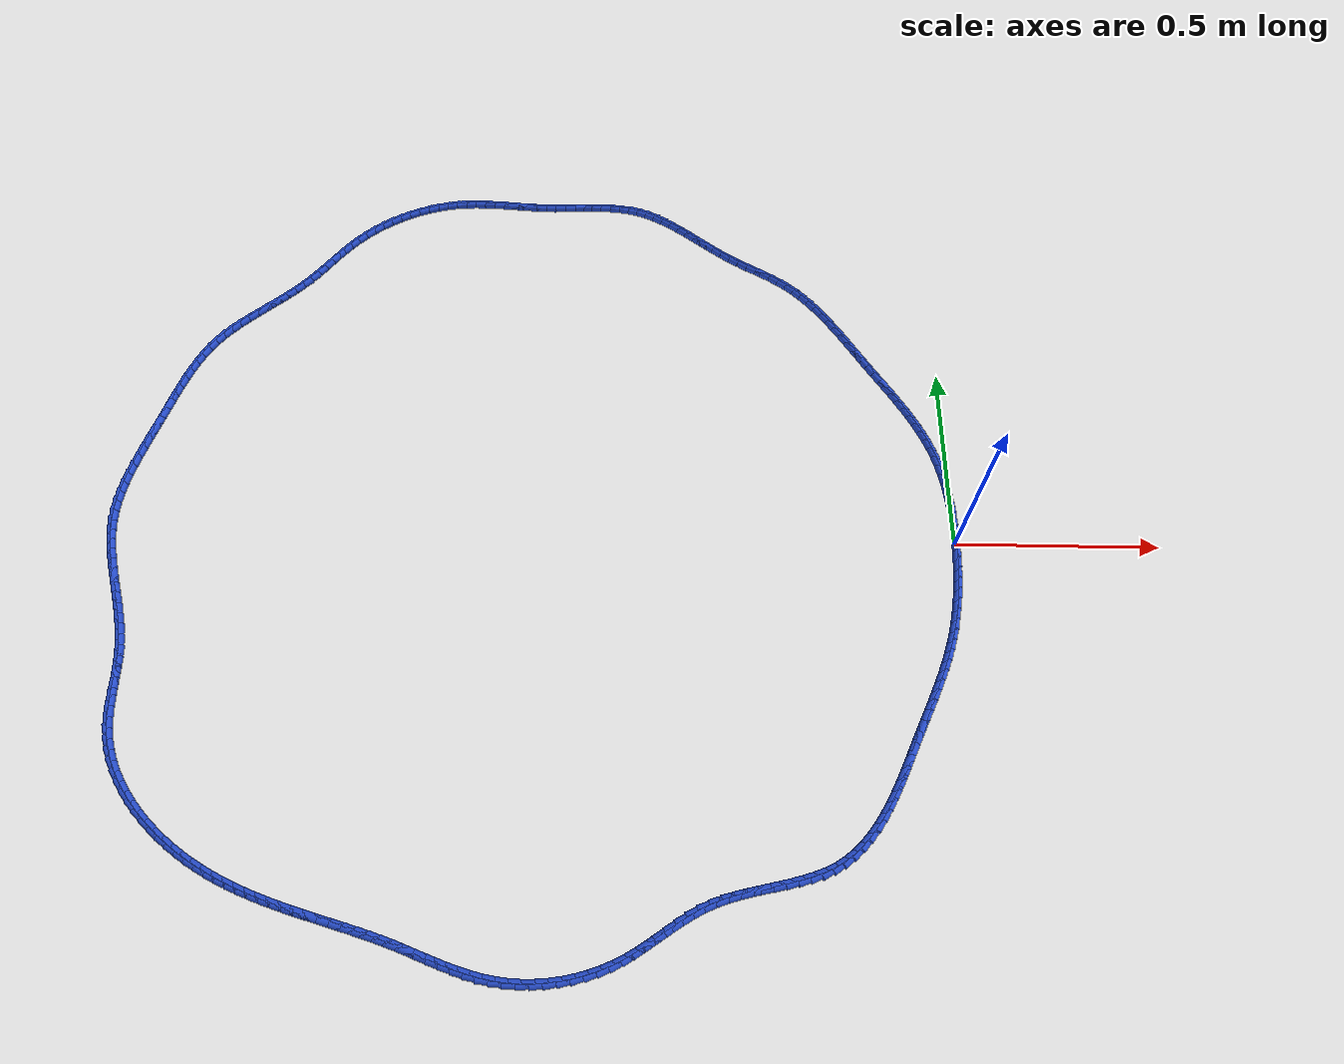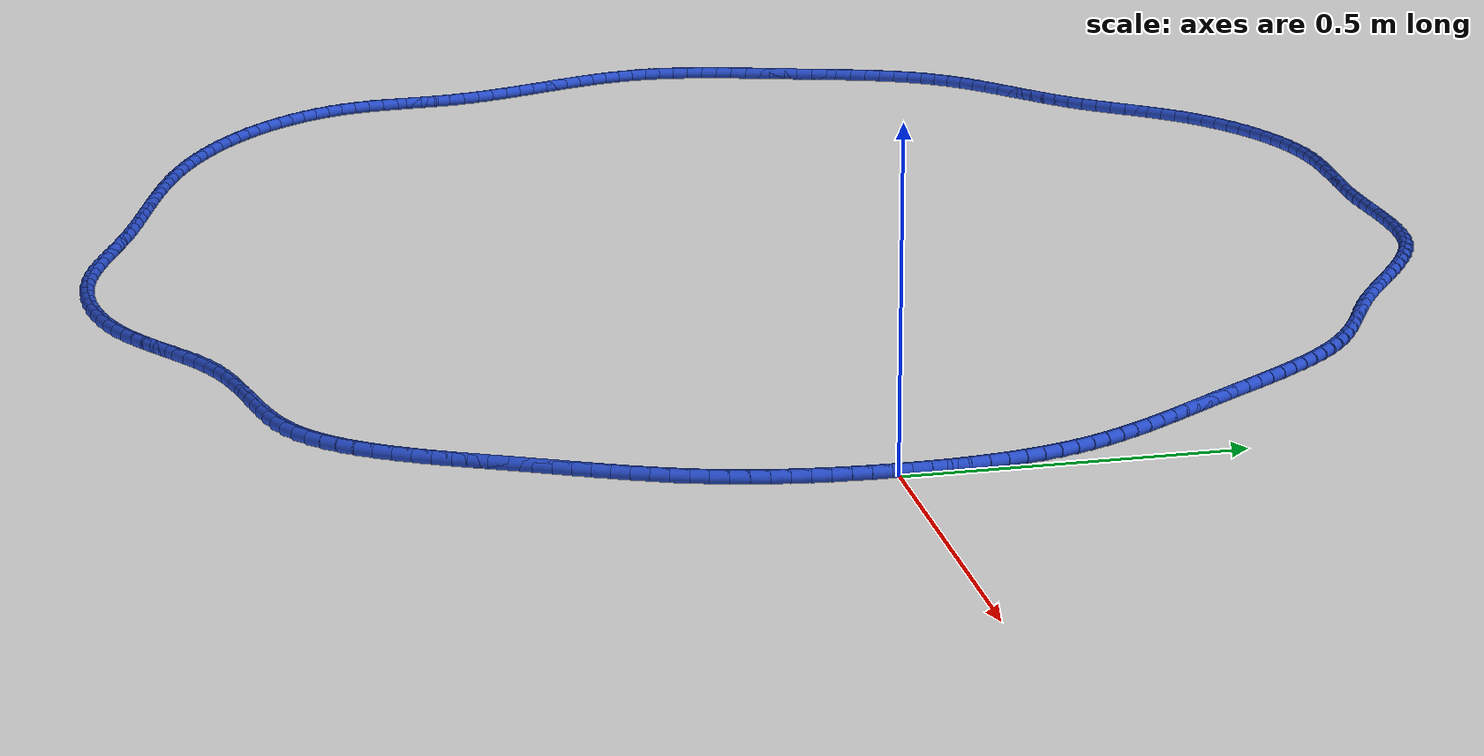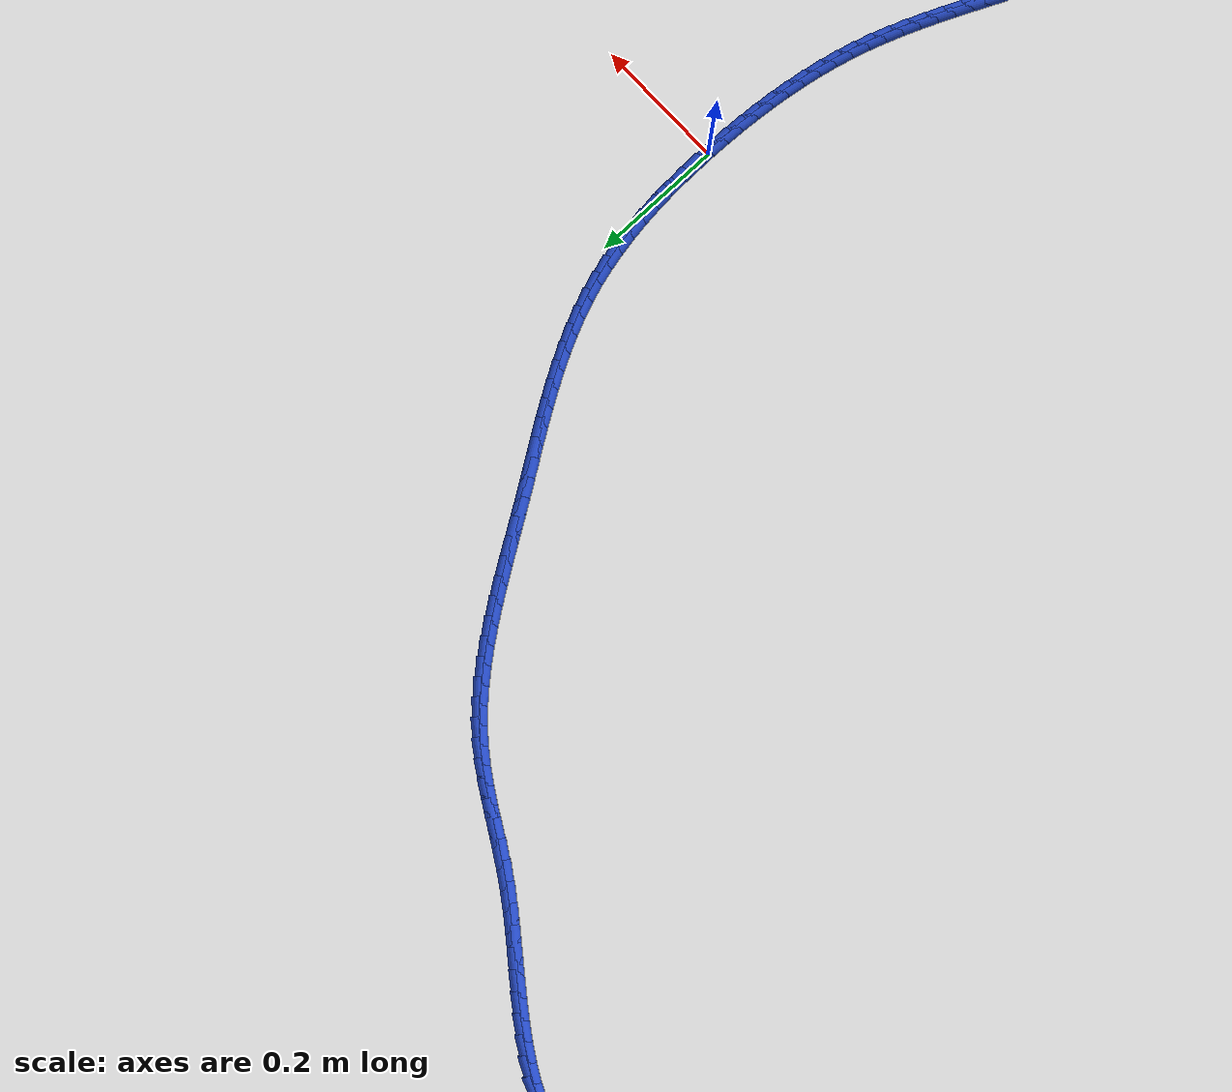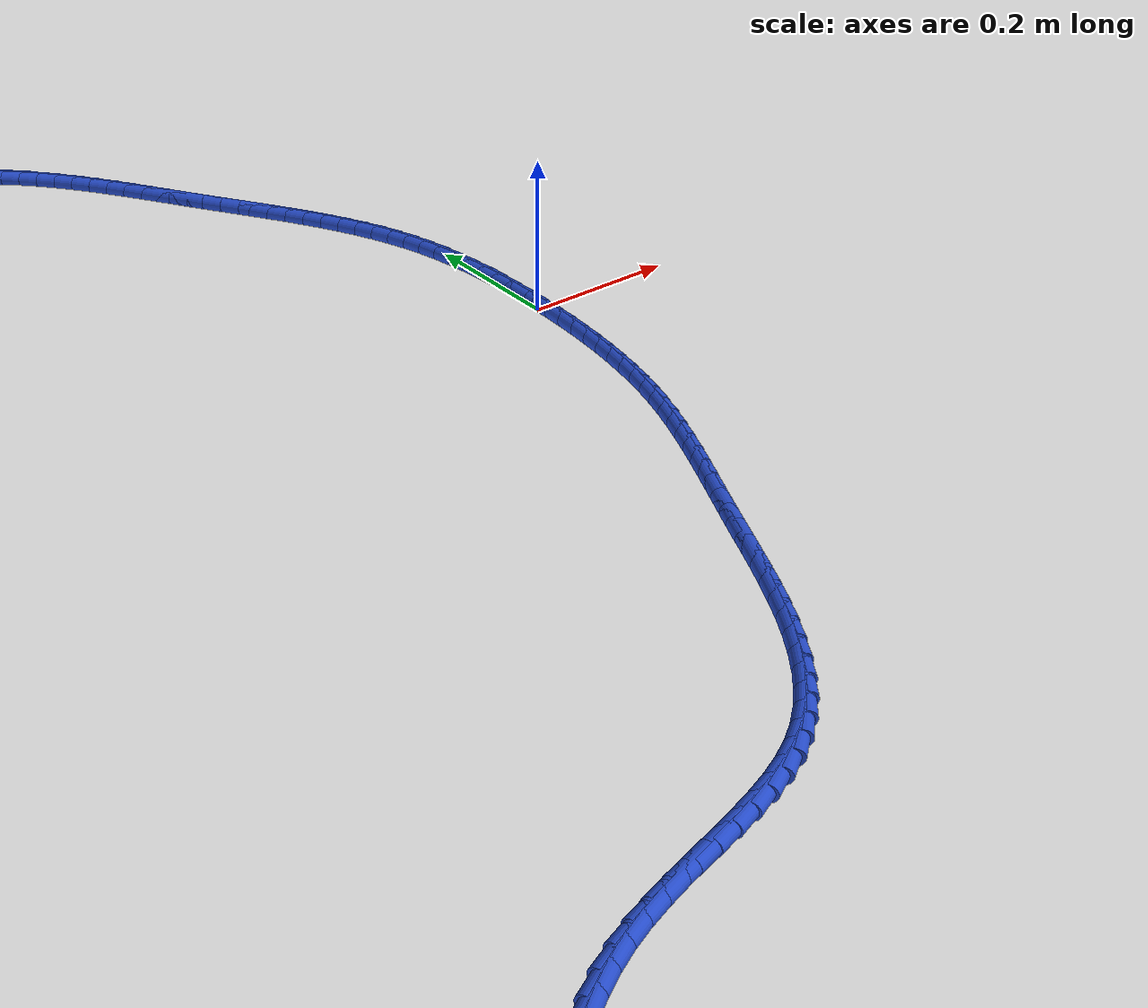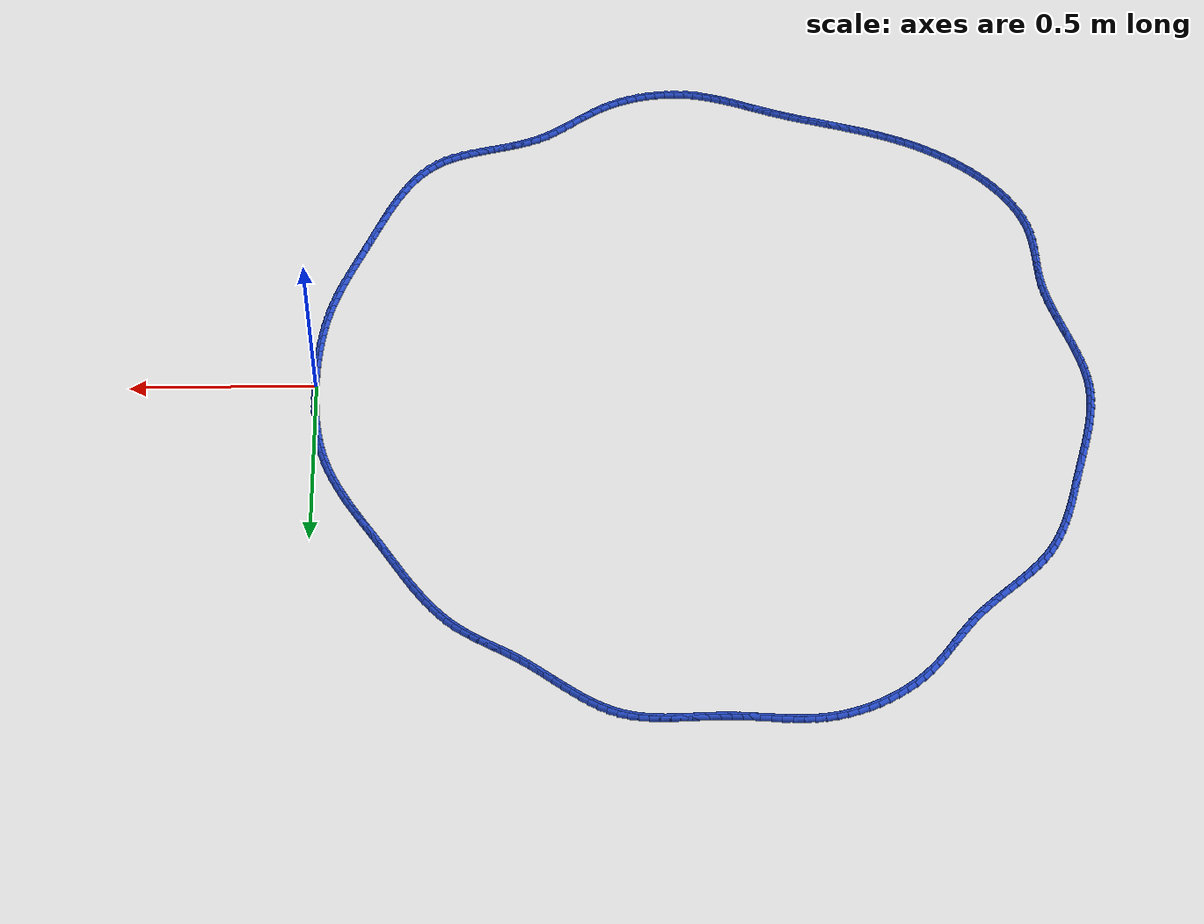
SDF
<sdf version="1.6">
 <world name="default">
  <light name="sun" type="directional">
   <pose>0 0 10 0 -0 0</pose>
   <diffuse>0.8 0.8 0.8 1</diffuse>
   <specular>0.2 0.2 0.2 1</specular>
   <attenuation>
    <range>1000</range>
    <constant>0.9</constant>
    <linear>0.01</linear>
    <quadratic>0.001</quadratic>
   </attenuation>
   <direction>-0.5 0.1 -0.9</direction>
  </light>
  <model name="ground_plane">
   <static>1</static>
   <link name="link">
    <collision name="collision">
     <geometry><plane><normal>0 0 1</normal><size>100 100</size></plane></geometry>
     <surface><friction><ode><mu>100</mu><mu2>50</mu2></ode></friction></surface>
    </collision>
    <visual name="visual">
     <cast_shadows>0</cast_shadows>
     <geometry><plane><normal>0 0 1</normal><size>100 100</size></plane></geometry>
     <material>
      <script><uri>file://media/materials/scripts/gazebo.material</uri><name>Gazebo/WhiteGlow</name></script>
     </material>
    </visual>
   </link>
  </model>
  <gravity>0 0 -9.8</gravity>
  <magnetic_field>6e-06 2.3e-05 -4.2e-05</magnetic_field>
  <atmosphere type="adiabatic"/>
  <physics name="default_physics" default="0" type="ode">
   <max_step_size>0.001</max_step_size>
   <real_time_factor>1</real_time_factor>
   <real_time_update_rate>1000</real_time_update_rate>
  </physics>
  <scene><ambient>0.4 0.4 0.4 1</ambient><background>0.7 0.7 0.7 1</background><shadows>1</shadows></scene>
  <spherical_coordinates>
   <surface_model>EARTH_WGS84</surface_model>
   <latitude_deg>0</latitude_deg>
   <longitude_deg>0</longitude_deg>
   <elevation>0</elevation>
   <heading_deg>0</heading_deg>
  </spherical_coordinates>
  <model name="line">
   <link name="link_0">
    <pose>-7.37257477290143e-18 3.469446951953614e-17 0.01 0 1.57 1.570679695974858</pose>
    <collision name="collision">
     <geometry><cylinder><radius>0.01</radius><length>0.08</length></cylinder></geometry>
    </collision>
    <visual name="visual">
     <material>
      <script><name>Gazebo/Blue</name><uri>file://media/materials/scripts/gazebo.material</uri></script>
     </material>
     <geometry><cylinder><radius>0.01</radius><length>0.08</length></cylinder></geometry>
    </visual>
   </link>
   <link name="link_1">
    <pose>3.250097629793035e-06 0.027866541742451803 0.01 0 1.57 -1.5481850060267832</pose>
    <collision name="collision">
     <geometry><cylinder><radius>0.01</radius><length>0.08</length></cylinder></geometry>
    </collision>
    <visual name="visual">
     <material>
      <script><name>Gazebo/Blue</name><uri>file://media/materials/scripts/gazebo.material</uri></script>
     </material>
     <geometry><cylinder><radius>0.01</radius><length>0.08</length></cylinder></geometry>
    </visual>
   </link>
   <link name="link_2">
    <pose>-0.0006263920770606841 0.05570812036526805 0.01 0 1.57 -1.5224213287298272</pose>
    <collision name="collision">
     <geometry><cylinder><radius>0.01</radius><length>0.08</length></cylinder></geometry>
    </collision>
    <visual name="visual">
     <material>
      <script><name>Gazebo/Blue</name><uri>file://media/materials/scripts/gazebo.material</uri></script>
     </material>
     <geometry><cylinder><radius>0.01</radius><length>0.08</length></cylinder></geometry>
    </visual>
   </link>
   <link name="link_3">
    <pose>-0.0019702294024981047 0.08346603167380513 0.01 0 1.57 -1.4934822107434715</pose>
    <collision name="collision">
     <geometry><cylinder><radius>0.01</radius><length>0.08</length></cylinder></geometry>
    </collision>
    <visual name="visual">
     <material>
      <script><name>Gazebo/Blue</name><uri>file://media/materials/scripts/gazebo.material</uri></script>
     </material>
     <geometry><cylinder><radius>0.01</radius><length>0.08</length></cylinder></geometry>
    </visual>
   </link>
   <link name="link_4">
    <pose>-0.004109564757109139 0.11108157147341934 0.01 0 1.57 -1.461217150091305</pose>
    <collision name="collision">
     <geometry><cylinder><radius>0.01</radius><length>0.08</length></cylinder></geometry>
    </collision>
    <visual name="visual">
     <material>
      <script><name>Gazebo/Blue</name><uri>file://media/materials/scripts/gazebo.material</uri></script>
     </material>
     <geometry><cylinder><radius>0.01</radius><length>0.08</length></cylinder></geometry>
    </visual>
   </link>
   <link name="link_5">
    <pose>-0.007125701019320453 0.13849603556946702 0.01 0 1.57 -1.425472477816047</pose>
    <collision name="collision">
     <geometry><cylinder><radius>0.01</radius><length>0.08</length></cylinder></geometry>
    </collision>
    <visual name="visual">
     <material>
      <script><name>Gazebo/Blue</name><uri>file://media/materials/scripts/gazebo.material</uri></script>
     </material>
     <geometry><cylinder><radius>0.01</radius><length>0.08</length></cylinder></geometry>
    </visual>
   </link>
   <link name="link_6">
    <pose>-0.011099941067558721 0.16565071976730453 0.01 0 1.57 -1.3861014814704375</pose>
    <collision name="collision">
     <geometry><cylinder><radius>0.01</radius><length>0.08</length></cylinder></geometry>
    </collision>
    <visual name="visual">
     <material>
      <script><name>Gazebo/Blue</name><uri>file://media/materials/scripts/gazebo.material</uri></script>
     </material>
     <geometry><cylinder><radius>0.01</radius><length>0.08</length></cylinder></geometry>
    </visual>
   </link>
   <link name="link_7">
    <pose>-0.016113587780250602 0.19248691987228828 0.01 0 1.57 -1.3429775391351089</pose>
    <collision name="collision">
     <geometry><cylinder><radius>0.01</radius><length>0.08</length></cylinder></geometry>
    </collision>
    <visual name="visual">
     <material>
      <script><name>Gazebo/Blue</name><uri>file://media/materials/scripts/gazebo.material</uri></script>
     </material>
     <geometry><cylinder><radius>0.01</radius><length>0.08</length></cylinder></geometry>
    </visual>
   </link>
   <link name="link_8">
    <pose>-0.02224794403582276 0.21894593168977436 0.01 0 1.57 -1.296010558039404</pose>
    <collision name="collision">
     <geometry><cylinder><radius>0.01</radius><length>0.08</length></cylinder></geometry>
    </collision>
    <visual name="visual">
     <material>
      <script><name>Gazebo/Blue</name><uri>file://media/materials/scripts/gazebo.material</uri></script>
     </material>
     <geometry><cylinder><radius>0.01</radius><length>0.08</length></cylinder></geometry>
    </visual>
   </link>
   <link name="link_9">
    <pose>-0.029584312712701878 0.2449690510251194 0.01 0 1.57 -1.2453110199539499</pose>
    <collision name="collision">
     <geometry><cylinder><radius>0.01</radius><length>0.08</length></cylinder></geometry>
    </collision>
    <visual name="visual">
     <material>
      <script><name>Gazebo/Blue</name><uri>file://media/materials/scripts/gazebo.material</uri></script>
     </material>
     <geometry><cylinder><radius>0.01</radius><length>0.08</length></cylinder></geometry>
    </visual>
   </link>
   <link name="link_10">
    <pose>-0.03820055091153638 0.2704995345184524 0.01 0 1.57 -1.1950090191509404</pose>
    <collision name="collision">
     <geometry><cylinder><radius>0.01</radius><length>0.08</length></cylinder></geometry>
    </collision>
    <visual name="visual">
     <material>
      <script><name>Gazebo/Blue</name><uri>file://media/materials/scripts/gazebo.material</uri></script>
     </material>
     <geometry><cylinder><radius>0.01</radius><length>0.08</length></cylinder></geometry>
    </visual>
   </link>
   <link name="link_11">
    <pose>-0.048078137748480035 0.29553548311951794 0.01 0 1.57 -1.1498620533162103</pose>
    <collision name="collision">
     <geometry><cylinder><radius>0.01</radius><length>0.08</length></cylinder></geometry>
    </collision>
    <visual name="visual">
     <material>
      <script><name>Gazebo/Blue</name><uri>file://media/materials/scripts/gazebo.material</uri></script>
     </material>
     <geometry><cylinder><radius>0.01</radius><length>0.08</length></cylinder></geometry>
    </visual>
   </link>
   <link name="link_12">
    <pose>-0.059091575274804346 0.32013587354028866 0.01 0 1.57 -1.1102996658686988</pose>
    <collision name="collision">
     <geometry><cylinder><radius>0.01</radius><length>0.08</length></cylinder></geometry>
    </collision>
    <visual name="visual">
     <material>
      <script><name>Gazebo/Blue</name><uri>file://media/materials/scripts/gazebo.material</uri></script>
     </material>
     <geometry><cylinder><radius>0.01</radius><length>0.08</length></cylinder></geometry>
    </visual>
   </link>
   <link name="link_13">
    <pose>-0.0711097927112542 0.34436285373609155 0.01 0 1.57 -1.0763937316885046</pose>
    <collision name="collision">
     <geometry><cylinder><radius>0.01</radius><length>0.08</length></cylinder></geometry>
    </collision>
    <visual name="visual">
     <material>
      <script><name>Gazebo/Blue</name><uri>file://media/materials/scripts/gazebo.material</uri></script>
     </material>
     <geometry><cylinder><radius>0.01</radius><length>0.08</length></cylinder></geometry>
    </visual>
   </link>
   <link name="link_14">
    <pose>-0.08400171927857454 0.36827857166225364 0.01 0 1.57 -1.0481283188922614</pose>
    <collision name="collision">
     <geometry><cylinder><radius>0.01</radius><length>0.08</length></cylinder></geometry>
    </collision>
    <visual name="visual">
     <material>
      <script><name>Gazebo/Blue</name><uri>file://media/materials/scripts/gazebo.material</uri></script>
     </material>
     <geometry><cylinder><radius>0.01</radius><length>0.08</length></cylinder></geometry>
    </visual>
   </link>
   <link name="link_15">
    <pose>-0.0976362841975103 0.391945175274102 0.01 0 1.57 -1.025432645575937</pose>
    <collision name="collision">
     <geometry><cylinder><radius>0.01</radius><length>0.08</length></cylinder></geometry>
    </collision>
    <visual name="visual">
     <material>
      <script><name>Gazebo/Blue</name><uri>file://media/materials/scripts/gazebo.material</uri></script>
     </material>
     <geometry><cylinder><radius>0.01</radius><length>0.08</length></cylinder></geometry>
    </visual>
   </link>
   <link name="link_16">
    <pose>-0.11188241668880641 0.4154248125269636 0.01 0 1.57 -1.0082083457703979</pose>
    <collision name="collision">
     <geometry><cylinder><radius>0.01</radius><length>0.08</length></cylinder></geometry>
    </collision>
    <visual name="visual">
     <material>
      <script><name>Gazebo/Blue</name><uri>file://media/materials/scripts/gazebo.material</uri></script>
     </material>
     <geometry><cylinder><radius>0.01</radius><length>0.08</length></cylinder></geometry>
    </visual>
   </link>
   <link name="link_17">
    <pose>-0.12660904597320788 0.4387796313761657 0.01 0 1.57 -0.9963503303364913</pose>
    <collision name="collision">
     <geometry><cylinder><radius>0.01</radius><length>0.08</length></cylinder></geometry>
    </collision>
    <visual name="visual">
     <material>
      <script><name>Gazebo/Blue</name><uri>file://media/materials/scripts/gazebo.material</uri></script>
     </material>
     <geometry><cylinder><radius>0.01</radius><length>0.08</length></cylinder></geometry>
    </visual>
   </link>
   <link name="link_18">
    <pose>-0.1416851012714595 0.4620717797770349 0.01 0 1.57 -0.9897615026237359</pose>
    <collision name="collision">
     <geometry><cylinder><radius>0.01</radius><length>0.08</length></cylinder></geometry>
    </collision>
    <visual name="visual">
     <material>
      <script><name>Gazebo/Blue</name><uri>file://media/materials/scripts/gazebo.material</uri></script>
     </material>
     <geometry><cylinder><radius>0.01</radius><length>0.08</length></cylinder></geometry>
    </visual>
   </link>
   <link name="link_19">
    <pose>-0.1569795118043063 0.48536340568489855 0.01 0 1.57 -0.9883620079748079</pose>
    <collision name="collision">
     <geometry><cylinder><radius>0.01</radius><length>0.08</length></cylinder></geometry>
    </collision>
    <visual name="visual">
     <material>
      <script><name>Gazebo/Blue</name><uri>file://media/materials/scripts/gazebo.material</uri></script>
     </material>
     <geometry><cylinder><radius>0.01</radius><length>0.08</length></cylinder></geometry>
    </visual>
   </link>
   <link name="link_20">
    <pose>-0.17236120679249317 0.5087166570550834 0.01 0 1.57 -0.9920937467896654</pose>
    <collision name="collision">
     <geometry><cylinder><radius>0.01</radius><length>0.08</length></cylinder></geometry>
    </collision>
    <visual name="visual">
     <material>
      <script><name>Gazebo/Blue</name><uri>file://media/materials/scripts/gazebo.material</uri></script>
     </material>
     <geometry><cylinder><radius>0.01</radius><length>0.08</length></cylinder></geometry>
    </visual>
   </link>
   <link name="link_21">
    <pose>-0.18769911545676507 0.5321936818429167 0.01 0 1.57 -0.9991754209376995</pose>
    <collision name="collision">
     <geometry><cylinder><radius>0.01</radius><length>0.08</length></cylinder></geometry>
    </collision>
    <visual name="visual">
     <material>
      <script><name>Gazebo/Blue</name><uri>file://media/materials/scripts/gazebo.material</uri></script>
     </material>
     <geometry><cylinder><radius>0.01</radius><length>0.08</length></cylinder></geometry>
    </visual>
   </link>
   <link name="link_22">
    <pose>-0.20290074613906134 0.5558259352618468 0.01 0 1.57 -1.002321091380189</pose>
    <collision name="collision">
     <geometry><cylinder><radius>0.01</radius><length>0.08</length></cylinder></geometry>
    </collision>
    <visual name="visual">
     <material>
      <script><name>Gazebo/Blue</name><uri>file://media/materials/scripts/gazebo.material</uri></script>
     </material>
     <geometry><cylinder><radius>0.01</radius><length>0.08</length></cylinder></geometry>
    </visual>
   </link>
   <link name="link_23">
    <pose>-0.2180348154502989 0.5795166185984492 0.01 0 1.57 -0.9996446439555562</pose>
    <collision name="collision">
     <geometry><cylinder><radius>0.01</radius><length>0.08</length></cylinder></geometry>
    </collision>
    <visual name="visual">
     <material>
      <script><name>Gazebo/Blue</name><uri>file://media/materials/scripts/gazebo.material</uri></script>
     </material>
     <geometry><cylinder><radius>0.01</radius><length>0.08</length></cylinder></geometry>
    </visual>
   </link>
   <link name="link_24">
    <pose>-0.2332121412699618 0.6031354382506432 0.01 0 1.57 -0.9911088656459692</pose>
    <collision name="collision">
     <geometry><cylinder><radius>0.01</radius><length>0.08</length></cylinder></geometry>
    </collision>
    <visual name="visual">
     <material>
      <script><name>Gazebo/Blue</name><uri>file://media/materials/scripts/gazebo.material</uri></script>
     </material>
     <geometry><cylinder><radius>0.01</radius><length>0.08</length></cylinder></geometry>
    </visual>
   </link>
   <link name="link_25">
    <pose>-0.24854354160202283 0.6265521005173063 0.01 0 1.57 -0.976616741418029</pose>
    <collision name="collision">
     <geometry><cylinder><radius>0.01</radius><length>0.08</length></cylinder></geometry>
    </collision>
    <visual name="visual">
     <material>
      <script><name>Gazebo/Blue</name><uri>file://media/materials/scripts/gazebo.material</uri></script>
     </material>
     <geometry><cylinder><radius>0.01</radius><length>0.08</length></cylinder></geometry>
    </visual>
   </link>
   <link name="link_26">
    <pose>-0.26413983445045536 0.6496363116973167 0.01 0 1.57 -0.9560180378007423</pose>
    <collision name="collision">
     <geometry><cylinder><radius>0.01</radius><length>0.08</length></cylinder></geometry>
    </collision>
    <visual name="visual">
     <material>
      <script><name>Gazebo/Blue</name><uri>file://media/materials/scripts/gazebo.material</uri></script>
     </material>
     <geometry><cylinder><radius>0.01</radius><length>0.08</length></cylinder></geometry>
    </visual>
   </link>
   <link name="link_27">
    <pose>-0.2801118378192323 0.672257778089552 0.01 0 1.57 -0.9291219481177067</pose>
    <collision name="collision">
     <geometry><cylinder><radius>0.01</radius><length>0.08</length></cylinder></geometry>
    </collision>
    <visual name="visual">
     <material>
      <script><name>Gazebo/Blue</name><uri>file://media/materials/scripts/gazebo.material</uri></script>
     </material>
     <geometry><cylinder><radius>0.01</radius><length>0.08</length></cylinder></geometry>
    </visual>
   </link>
   <link name="link_28">
    <pose>-0.2965703697123269 0.6942862059928905 0.01 0 1.57 -0.8957177045043702</pose>
    <collision name="collision">
     <geometry><cylinder><radius>0.01</radius><length>0.08</length></cylinder></geometry>
    </collision>
    <visual name="visual">
     <material>
      <script><name>Gazebo/Blue</name><uri>file://media/materials/scripts/gazebo.material</uri></script>
     </material>
     <geometry><cylinder><radius>0.01</radius><length>0.08</length></cylinder></geometry>
    </visual>
   </link>
   <link name="link_29">
    <pose>-0.31362624813371204 0.7155913017062093 0.01 0 1.57 -0.8556055141582676</pose>
    <collision name="collision">
     <geometry><cylinder><radius>0.01</radius><length>0.08</length></cylinder></geometry>
    </collision>
    <visual name="visual">
     <material>
      <script><name>Gazebo/Blue</name><uri>file://media/materials/scripts/gazebo.material</uri></script>
     </material>
     <geometry><cylinder><radius>0.01</radius><length>0.08</length></cylinder></geometry>
    </visual>
   </link>
   <link name="link_30">
    <pose>-0.33139029108736107 0.7360427715283873 0.01 0 1.57 -0.8086400053167925</pose>
    <collision name="collision">
     <geometry><cylinder><radius>0.01</radius><length>0.08</length></cylinder></geometry>
    </collision>
    <visual name="visual">
     <material>
      <script><name>Gazebo/Blue</name><uri>file://media/materials/scripts/gazebo.material</uri></script>
     </material>
     <geometry><cylinder><radius>0.01</radius><length>0.08</length></cylinder></geometry>
    </visual>
   </link>
   <link name="link_31">
    <pose>-0.3499733165772468 0.7555103217583014 0.01 0 1.57 -0.754787010417124</pose>
    <collision name="collision">
     <geometry><cylinder><radius>0.01</radius><length>0.08</length></cylinder></geometry>
    </collision>
    <visual name="visual">
     <material>
      <script><name>Gazebo/Blue</name><uri>file://media/materials/scripts/gazebo.material</uri></script>
     </material>
     <geometry><cylinder><radius>0.01</radius><length>0.08</length></cylinder></geometry>
    </visual>
   </link>
   <link name="link_32">
    <pose>-0.3694861426073427 0.77386365869483 0.01 0 1.57 -0.6941913041914025</pose>
    <collision name="collision">
     <geometry><cylinder><radius>0.01</radius><length>0.08</length></cylinder></geometry>
    </collision>
    <visual name="visual">
     <material>
      <script><name>Gazebo/Blue</name><uri>file://media/materials/scripts/gazebo.material</uri></script>
     </material>
     <geometry><cylinder><radius>0.01</radius><length>0.08</length></cylinder></geometry>
    </visual>
   </link>
   <link name="link_33">
    <pose>-0.3900395871816214 0.7909724886368507 0.01 0 1.57 -0.6302014020379919</pose>
    <collision name="collision">
     <geometry><cylinder><radius>0.01</radius><length>0.08</length></cylinder></geometry>
    </collision>
    <visual name="visual">
     <material>
      <script><name>Gazebo/Blue</name><uri>file://media/materials/scripts/gazebo.material</uri></script>
     </material>
     <geometry><cylinder><radius>0.01</radius><length>0.08</length></cylinder></geometry>
    </visual>
   </link>
   <link name="link_34">
    <pose>-0.41169835861751175 0.8067708999495686 0.01 0 1.57 -0.5784494462795001</pose>
    <collision name="collision">
     <geometry><cylinder><radius>0.01</radius><length>0.08</length></cylinder></geometry>
    </collision>
    <visual name="visual">
     <material>
      <script><name>Gazebo/Blue</name><uri>file://media/materials/scripts/gazebo.material</uri></script>
     </material>
     <geometry><cylinder><radius>0.01</radius><length>0.08</length></cylinder></geometry>
    </visual>
   </link>
   <link name="link_35">
    <pose>-0.4342909343584891 0.8215228256129579 0.01 0 1.57 -0.5437946530491432</pose>
    <collision name="collision">
     <geometry><cylinder><radius>0.01</radius><length>0.08</length></cylinder></geometry>
    </collision>
    <visual name="visual">
     <material>
      <script><name>Gazebo/Blue</name><uri>file://media/materials/scripts/gazebo.material</uri></script>
     </material>
     <geometry><cylinder><radius>0.01</radius><length>0.08</length></cylinder></geometry>
    </visual>
   </link>
   <link name="link_36">
    <pose>-0.4575703435077503 0.8355975456698783 0.01 0 1.57 -0.5258891914275329</pose>
    <collision name="collision">
     <geometry><cylinder><radius>0.01</radius><length>0.08</length></cylinder></geometry>
    </collision>
    <visual name="visual">
     <material>
      <script><name>Gazebo/Blue</name><uri>file://media/materials/scripts/gazebo.material</uri></script>
     </material>
     <geometry><cylinder><radius>0.01</radius><length>0.08</length></cylinder></geometry>
    </visual>
   </link>
   <link name="link_37">
    <pose>-0.48128958207280836 0.8493643863740566 0.01 0 1.57 -0.5243089317881079</pose>
    <collision name="collision">
     <geometry><cylinder><radius>0.01</radius><length>0.08</length></cylinder></geometry>
    </collision>
    <visual name="visual">
     <material>
      <script><name>Gazebo/Blue</name><uri>file://media/materials/scripts/gazebo.material</uri></script>
     </material>
     <geometry><cylinder><radius>0.01</radius><length>0.08</length></cylinder></geometry>
    </visual>
   </link>
   <link name="link_38">
    <pose>-0.5052016460611755 0.8631926739792186 0.01 0 1.57 -0.538701983099247</pose>
    <collision name="collision">
     <geometry><cylinder><radius>0.01</radius><length>0.08</length></cylinder></geometry>
    </collision>
    <visual name="visual">
     <material>
      <script><name>Gazebo/Blue</name><uri>file://media/materials/scripts/gazebo.material</uri></script>
     </material>
     <geometry><cylinder><radius>0.01</radius><length>0.08</length></cylinder></geometry>
    </visual>
   </link>
   <link name="link_39">
    <pose>-0.5290595314803646 0.8774517347390913 0.01 0 1.57 -0.5686784447791046</pose>
    <collision name="collision">
     <geometry><cylinder><radius>0.01</radius><length>0.08</length></cylinder></geometry>
    </collision>
    <visual name="visual">
     <material>
      <script><name>Gazebo/Blue</name><uri>file://media/materials/scripts/gazebo.material</uri></script>
     </material>
     <geometry><cylinder><radius>0.01</radius><length>0.08</length></cylinder></geometry>
    </visual>
   </link>
   <link name="link_40">
    <pose>-0.5526177854610032 0.8925079473684406 0.01 0 1.57 -0.6046107597396618</pose>
    <collision name="collision">
     <geometry><cylinder><radius>0.01</radius><length>0.08</length></cylinder></geometry>
    </collision>
    <visual name="visual">
     <material>
      <script><name>Gazebo/Blue</name><uri>file://media/materials/scripts/gazebo.material</uri></script>
     </material>
     <geometry><cylinder><radius>0.01</radius><length>0.08</length></cylinder></geometry>
    </visual>
   </link>
   <link name="link_41">
    <pose>-0.5757541886841246 0.9084935146566299 0.01 0 1.57 -0.6305902891140529</pose>
    <collision name="collision">
     <geometry><cylinder><radius>0.01</radius><length>0.08</length></cylinder></geometry>
    </collision>
    <visual name="visual">
     <material>
      <script><name>Gazebo/Blue</name><uri>file://media/materials/scripts/gazebo.material</uri></script>
     </material>
     <geometry><cylinder><radius>0.01</radius><length>0.08</length></cylinder></geometry>
    </visual>
   </link>
   <link name="link_42">
    <pose>-0.5985572550843227 0.9251401911830659 0.01 0 1.57 -0.6453732193261358</pose>
    <collision name="collision">
     <geometry><cylinder><radius>0.01</radius><length>0.08</length></cylinder></geometry>
    </collision>
    <visual name="visual">
     <material>
      <script><name>Gazebo/Blue</name><uri>file://media/materials/scripts/gazebo.material</uri></script>
     </material>
     <geometry><cylinder><radius>0.01</radius><length>0.08</length></cylinder></geometry>
    </visual>
   </link>
   <link name="link_43">
    <pose>-0.6211361447183626 0.9421404985037667 0.01 0 1.57 -0.6491340194506082</pose>
    <collision name="collision">
     <geometry><cylinder><radius>0.01</radius><length>0.08</length></cylinder></geometry>
    </collision>
    <visual name="visual">
     <material>
      <script><name>Gazebo/Blue</name><uri>file://media/materials/scripts/gazebo.material</uri></script>
     </material>
     <geometry><cylinder><radius>0.01</radius><length>0.08</length></cylinder></geometry>
    </visual>
   </link>
   <link name="link_44">
    <pose>-0.6436000176430091 0.9591869581747495 0.01 0 1.57 -0.6418353800522637</pose>
    <collision name="collision">
     <geometry><cylinder><radius>0.01</radius><length>0.08</length></cylinder></geometry>
    </collision>
    <visual name="visual">
     <material>
      <script><name>Gazebo/Blue</name><uri>file://media/materials/scripts/gazebo.material</uri></script>
     </material>
     <geometry><cylinder><radius>0.01</radius><length>0.08</length></cylinder></geometry>
    </visual>
   </link>
   <link name="link_45">
    <pose>-0.6660580339150276 0.9759720917520331 0.01 0 1.57 -0.6232104508540871</pose>
    <collision name="collision">
     <geometry><cylinder><radius>0.01</radius><length>0.08</length></cylinder></geometry>
    </collision>
    <visual name="visual">
     <material>
      <script><name>Gazebo/Blue</name><uri>file://media/materials/scripts/gazebo.material</uri></script>
     </material>
     <geometry><cylinder><radius>0.01</radius><length>0.08</length></cylinder></geometry>
    </visual>
   </link>
   <link name="link_46">
    <pose>-0.6886193535911824 0.9921884207916343 0.01 0 1.57 -0.5927759513215365</pose>
    <collision name="collision">
     <geometry><cylinder><radius>0.01</radius><length>0.08</length></cylinder></geometry>
    </collision>
    <visual name="visual">
     <material>
      <script><name>Gazebo/Blue</name><uri>file://media/materials/scripts/gazebo.material</uri></script>
     </material>
     <geometry><cylinder><radius>0.01</radius><length>0.08</length></cylinder></geometry>
    </visual>
   </link>
   <link name="link_47">
    <pose>-0.7113931367282395 1.0075284668495716 0.01 0 1.57 -0.5498857710418007</pose>
    <collision name="collision">
     <geometry><cylinder><radius>0.01</radius><length>0.08</length></cylinder></geometry>
    </collision>
    <visual name="visual">
     <material>
      <script><name>Gazebo/Blue</name><uri>file://media/materials/scripts/gazebo.material</uri></script>
     </material>
     <geometry><cylinder><radius>0.01</radius><length>0.08</length></cylinder></geometry>
    </visual>
   </link>
   <link name="link_48">
    <pose>-0.7344885433829633 1.0216847514818626 0.01 0 1.57 -0.4938456779371377</pose>
    <collision name="collision">
     <geometry><cylinder><radius>0.01</radius><length>0.08</length></cylinder></geometry>
    </collision>
    <visual name="visual">
     <material>
      <script><name>Gazebo/Blue</name><uri>file://media/materials/scripts/gazebo.material</uri></script>
     </material>
     <geometry><cylinder><radius>0.01</radius><length>0.08</length></cylinder></geometry>
    </visual>
   </link>
   <link name="link_49">
    <pose>-0.7580147336121185 1.0343497962445247 0.01 0 1.57 -0.4241167461615771</pose>
    <collision name="collision">
     <geometry><cylinder><radius>0.01</radius><length>0.08</length></cylinder></geometry>
    </collision>
    <visual name="visual">
     <material>
      <script><name>Gazebo/Blue</name><uri>file://media/materials/scripts/gazebo.material</uri></script>
     </material>
     <geometry><cylinder><radius>0.01</radius><length>0.08</length></cylinder></geometry>
    </visual>
   </link>
   <link name="link_50">
    <pose>-0.7820808674724711 1.0452161226935766 0.01 0 1.57 -0.3406269758845627</pose>
    <collision name="collision">
     <geometry><cylinder><radius>0.01</radius><length>0.08</length></cylinder></geometry>
    </collision>
    <visual name="visual">
     <material>
      <script><name>Gazebo/Blue</name><uri>file://media/materials/scripts/gazebo.material</uri></script>
     </material>
     <geometry><cylinder><radius>0.01</radius><length>0.08</length></cylinder></geometry>
    </visual>
   </link>
   <link name="link_51">
    <pose>-0.8067961050207851 1.0539762523850351 0.01 0 1.57 -0.2469386619011326</pose>
    <collision name="collision">
     <geometry><cylinder><radius>0.01</radius><length>0.08</length></cylinder></geometry>
    </collision>
    <visual name="visual">
     <material>
      <script><name>Gazebo/Blue</name><uri>file://media/materials/scripts/gazebo.material</uri></script>
     </material>
     <geometry><cylinder><radius>0.01</radius><length>0.08</length></cylinder></geometry>
    </visual>
   </link>
   <link name="link_52">
    <pose>-0.8322478464903049 1.0603922170231106 0.01 0 1.57 -0.16188282956521138</pose>
    <collision name="collision">
     <geometry><cylinder><radius>0.01</radius><length>0.08</length></cylinder></geometry>
    </collision>
    <visual name="visual">
     <material>
      <script><name>Gazebo/Blue</name><uri>file://media/materials/scripts/gazebo.material</uri></script>
     </material>
     <geometry><cylinder><radius>0.01</radius><length>0.08</length></cylinder></geometry>
    </visual>
   </link>
   <link name="link_53">
    <pose>-0.8583873008118371 1.0646611013631295 0.01 0 1.57 -0.09278360831525811</pose>
    <collision name="collision">
     <geometry><cylinder><radius>0.01</radius><length>0.08</length></cylinder></geometry>
    </collision>
    <visual name="visual">
     <material>
      <script><name>Gazebo/Blue</name><uri>file://media/materials/scripts/gazebo.material</uri></script>
     </material>
     <geometry><cylinder><radius>0.01</radius><length>0.08</length></cylinder></geometry>
    </visual>
   </link>
   <link name="link_54">
    <pose>-0.8851130955607902 1.0671479574144882 0.01 0 1.57 -0.03931135255314148</pose>
    <collision name="collision">
     <geometry><cylinder><radius>0.01</radius><length>0.08</length></cylinder></geometry>
    </collision>
    <visual name="visual">
     <material>
      <script><name>Gazebo/Blue</name><uri>file://media/materials/scripts/gazebo.material</uri></script>
     </material>
     <geometry><cylinder><radius>0.01</radius><length>0.08</length></cylinder></geometry>
    </visual>
   </link>
   <link name="link_55">
    <pose>-0.9123237459095317 1.0682181962497892 0.01 0 1.57 -0.0006897395904578615</pose>
    <collision name="collision">
     <geometry><cylinder><radius>0.01</radius><length>0.08</length></cylinder></geometry>
    </collision>
    <visual name="visual">
     <material>
      <script><name>Gazebo/Blue</name><uri>file://media/materials/scripts/gazebo.material</uri></script>
     </material>
     <geometry><cylinder><radius>0.01</radius><length>0.08</length></cylinder></geometry>
    </visual>
   </link>
   <link name="link_56">
    <pose>-0.9399177670304291 1.0682372289416344 0.01 0 1.57 0.02391438836098097</pose>
    <collision name="collision">
     <geometry><cylinder><radius>0.01</radius><length>0.08</length></cylinder></geometry>
    </collision>
    <visual name="visual">
     <material>
      <script><name>Gazebo/Blue</name><uri>file://media/materials/scripts/gazebo.material</uri></script>
     </material>
     <geometry><cylinder><radius>0.01</radius><length>0.08</length></cylinder></geometry>
    </visual>
   </link>
   <link name="link_57">
    <pose>-0.9677936740958498 1.067570466562627 0.01 0 1.57 0.03516996349496396</pose>
    <collision name="collision">
     <geometry><cylinder><radius>0.01</radius><length>0.08</length></cylinder></geometry>
    </collision>
    <visual name="visual">
     <material>
      <script><name>Gazebo/Blue</name><uri>file://media/materials/scripts/gazebo.material</uri></script>
     </material>
     <geometry><cylinder><radius>0.01</radius><length>0.08</length></cylinder></geometry>
    </visual>
   </link>
   <link name="link_58">
    <pose>-0.9958499822781617 1.0665833201853692 0.01 0 1.57 0.03347289503657778</pose>
    <collision name="collision">
     <geometry><cylinder><radius>0.01</radius><length>0.08</length></cylinder></geometry>
    </collision>
    <visual name="visual">
     <material>
      <script><name>Gazebo/Blue</name><uri>file://media/materials/scripts/gazebo.material</uri></script>
     </material>
     <geometry><cylinder><radius>0.01</radius><length>0.08</length></cylinder></geometry>
    </visual>
   </link>
   <link name="link_59">
    <pose>-1.0239852067497317 1.065641200882463 0.01 0 1.57 0.018910265171746717</pose>
    <collision name="collision">
     <geometry><cylinder><radius>0.01</radius><length>0.08</length></cylinder></geometry>
    </collision>
    <visual name="visual">
     <material>
      <script><name>Gazebo/Blue</name><uri>file://media/materials/scripts/gazebo.material</uri></script>
     </material>
     <geometry><cylinder><radius>0.01</radius><length>0.08</length></cylinder></geometry>
    </visual>
   </link>
   <link name="link_60">
    <pose>-1.052097862682928 1.065109519726511 0.01 0 1.57 -0.008601707539249446</pose>
    <collision name="collision">
     <geometry><cylinder><radius>0.01</radius><length>0.08</length></cylinder></geometry>
    </collision>
    <visual name="visual">
     <material>
      <script><name>Gazebo/Blue</name><uri>file://media/materials/scripts/gazebo.material</uri></script>
     </material>
     <geometry><cylinder><radius>0.01</radius><length>0.08</length></cylinder></geometry>
    </visual>
   </link>
   <link name="link_61">
    <pose>-1.080087070618817 1.0653502806453765 0.01 0 1.57 -0.04068234405713966</pose>
    <collision name="collision">
     <geometry><cylinder><radius>0.01</radius><length>0.08</length></cylinder></geometry>
    </collision>
    <visual name="visual">
     <material>
      <script><name>Gazebo/Blue</name><uri>file://media/materials/scripts/gazebo.material</uri></script>
     </material>
     <geometry><cylinder><radius>0.01</radius><length>0.08</length></cylinder></geometry>
    </visual>
   </link>
   <link name="link_62">
    <pose>-1.1078951767886323 1.0664822041215596 0.01 0 1.57 -0.0628856921022526</pose>
    <collision name="collision">
     <geometry><cylinder><radius>0.01</radius><length>0.08</length></cylinder></geometry>
    </collision>
    <visual name="visual">
     <material>
      <script><name>Gazebo/Blue</name><uri>file://media/materials/scripts/gazebo.material</uri></script>
     </material>
     <geometry><cylinder><radius>0.01</radius><length>0.08</length></cylinder></geometry>
    </visual>
   </link>
   <link name="link_63">
    <pose>-1.1355358306674401 1.0682227007045482 0.01 0 1.57 -0.07366438019306934</pose>
    <collision name="collision">
     <geometry><cylinder><radius>0.01</radius><length>0.08</length></cylinder></geometry>
    </collision>
    <visual name="visual">
     <material>
      <script><name>Gazebo/Blue</name><uri>file://media/materials/scripts/gazebo.material</uri></script>
     </material>
     <geometry><cylinder><radius>0.01</radius><length>0.08</length></cylinder></geometry>
    </visual>
   </link>
   <link name="link_64">
    <pose>-1.1630293474361602 1.0702516649231524 0.01 0 1.57 -0.07285466291696208</pose>
    <collision name="collision">
     <geometry><cylinder><radius>0.01</radius><length>0.08</length></cylinder></geometry>
    </collision>
    <visual name="visual">
     <material>
      <script><name>Gazebo/Blue</name><uri>file://media/materials/scripts/gazebo.material</uri></script>
     </material>
     <geometry><cylinder><radius>0.01</radius><length>0.08</length></cylinder></geometry>
    </visual>
   </link>
   <link name="link_65">
    <pose>-1.1903960422757134 1.0722489913061835 0.01 0 1.57 -0.06029263548911606</pose>
    <collision name="collision">
     <geometry><cylinder><radius>0.01</radius><length>0.08</length></cylinder></geometry>
    </collision>
    <visual name="visual">
     <material>
      <script><name>Gazebo/Blue</name><uri>file://media/materials/scripts/gazebo.material</uri></script>
     </material>
     <geometry><cylinder><radius>0.01</radius><length>0.08</length></cylinder></geometry>
    </visual>
   </link>
   <link name="link_66">
    <pose>-1.2176562303670206 1.0738945743824517 0.01 0 1.57 -0.03581798692901086</pose>
    <collision name="collision">
     <geometry><cylinder><radius>0.01</radius><length>0.08</length></cylinder></geometry>
    </collision>
    <visual name="visual">
     <material>
      <script><name>Gazebo/Blue</name><uri>file://media/materials/scripts/gazebo.material</uri></script>
     </material>
     <geometry><cylinder><radius>0.01</radius><length>0.08</length></cylinder></geometry>
    </visual>
   </link>
   <link name="link_67">
    <pose>-1.2448302268910023 1.0748683086807689 0.01 0 1.57 0.0006721214155758735</pose>
    <collision name="collision">
     <geometry><cylinder><radius>0.01</radius><length>0.08</length></cylinder></geometry>
    </collision>
    <visual name="visual">
     <material>
      <script><name>Gazebo/Blue</name><uri>file://media/materials/scripts/gazebo.material</uri></script>
     </material>
     <geometry><cylinder><radius>0.01</radius><length>0.08</length></cylinder></geometry>
    </visual>
   </link>
   <link name="link_68">
    <pose>-1.2719383470285779 1.0748500887299448 0.01 0 1.57 0.04911618964584172</pose>
    <collision name="collision">
     <geometry><cylinder><radius>0.01</radius><length>0.08</length></cylinder></geometry>
    </collision>
    <visual name="visual">
     <material>
      <script><name>Gazebo/Blue</name><uri>file://media/materials/scripts/gazebo.material</uri></script>
     </material>
     <geometry><cylinder><radius>0.01</radius><length>0.08</length></cylinder></geometry>
    </visual>
   </link>
   <link name="link_69">
    <pose>-1.2990009059606693 1.073519809058791 0.01 0 1.57 0.10910869469622773</pose>
    <collision name="collision">
     <geometry><cylinder><radius>0.01</radius><length>0.08</length></cylinder></geometry>
    </collision>
    <visual name="visual">
     <material>
      <script><name>Gazebo/Blue</name><uri>file://media/materials/scripts/gazebo.material</uri></script>
     </material>
     <geometry><cylinder><radius>0.01</radius><length>0.08</length></cylinder></geometry>
    </visual>
   </link>
   <link name="link_70">
    <pose>-1.3260379578470167 1.0705580693996026 0.01 0 1.57 0.17586983145418683</pose>
    <collision name="collision">
     <geometry><cylinder><radius>0.01</radius><length>0.08</length></cylinder></geometry>
    </collision>
    <visual name="visual">
     <material>
      <script><name>Gazebo/Blue</name><uri>file://media/materials/scripts/gazebo.material</uri></script>
     </material>
     <geometry><cylinder><radius>0.01</radius><length>0.08</length></cylinder></geometry>
    </visual>
   </link>
   <link name="link_71">
    <pose>-1.3530263998001533 1.0657620673027055 0.01 0 1.57 0.24079997842728526</pose>
    <collision name="collision">
     <geometry><cylinder><radius>0.01</radius><length>0.08</length></cylinder></geometry>
    </collision>
    <visual name="visual">
     <material>
      <script><name>Gazebo/Blue</name><uri>file://media/materials/scripts/gazebo.material</uri></script>
     </material>
     <geometry><cylinder><radius>0.01</radius><length>0.08</length></cylinder></geometry>
    </visual>
   </link>
   <link name="link_72">
    <pose>-1.3798522275476073 1.0591745894825129 0.01 0 1.57 0.3032984700191152</pose>
    <collision name="collision">
     <geometry><cylinder><radius>0.01</radius><length>0.08</length></cylinder></geometry>
    </collision>
    <visual name="visual">
     <material>
      <script><name>Gazebo/Blue</name><uri>file://media/materials/scripts/gazebo.material</uri></script>
     </material>
     <geometry><cylinder><radius>0.01</radius><length>0.08</length></cylinder></geometry>
    </visual>
   </link>
   <link name="link_73">
    <pose>-1.4063899311477015 1.0508695076328594 0.01 0 1.57 0.3638715725081384</pose>
    <collision name="collision">
     <geometry><cylinder><radius>0.01</radius><length>0.08</length></cylinder></geometry>
    </collision>
    <visual name="visual">
     <material>
      <script><name>Gazebo/Blue</name><uri>file://media/materials/scripts/gazebo.material</uri></script>
     </material>
     <geometry><cylinder><radius>0.01</radius><length>0.08</length></cylinder></geometry>
    </visual>
   </link>
   <link name="link_74">
    <pose>-1.4325140006587587 1.04092069344758 0.01 0 1.57 0.4230313280591888</pose>
    <collision name="collision">
     <geometry><cylinder><radius>0.01</radius><length>0.08</length></cylinder></geometry>
    </collision>
    <visual name="visual">
     <material>
      <script><name>Gazebo/Blue</name><uri>file://media/materials/scripts/gazebo.material</uri></script>
     </material>
     <geometry><cylinder><radius>0.01</radius><length>0.08</length></cylinder></geometry>
    </visual>
   </link>
   <link name="link_75">
    <pose>-1.4580989261391004 1.02940201862051 0.01 0 1.57 0.48129039509841565</pose>
    <collision name="collision">
     <geometry><cylinder><radius>0.01</radius><length>0.08</length></cylinder></geometry>
    </collision>
    <visual name="visual">
     <material>
      <script><name>Gazebo/Blue</name><uri>file://media/materials/scripts/gazebo.material</uri></script>
     </material>
     <geometry><cylinder><radius>0.01</radius><length>0.08</length></cylinder></geometry>
    </visual>
   </link>
   <link name="link_76">
    <pose>-1.4830191976470493 1.0163873548454838 0.01 0 1.57 0.5391605565181522</pose>
    <collision name="collision">
     <geometry><cylinder><radius>0.01</radius><length>0.08</length></cylinder></geometry>
    </collision>
    <visual name="visual">
     <material>
      <script><name>Gazebo/Blue</name><uri>file://media/materials/scripts/gazebo.material</uri></script>
     </material>
     <geometry><cylinder><radius>0.01</radius><length>0.08</length></cylinder></geometry>
    </visual>
   </link>
   <link name="link_77">
    <pose>-1.5071493052409286 1.0019505738163368 0.01 0 1.57 0.5971534359102952</pose>
    <collision name="collision">
     <geometry><cylinder><radius>0.01</radius><length>0.08</length></cylinder></geometry>
    </collision>
    <visual name="visual">
     <material>
      <script><name>Gazebo/Blue</name><uri>file://media/materials/scripts/gazebo.material</uri></script>
     </material>
     <geometry><cylinder><radius>0.01</radius><length>0.08</length></cylinder></geometry>
    </visual>
   </link>
   <link name="link_78">
    <pose>-1.5303637389790599 0.986165547226903 0.01 0 1.57 0.6557821618054867</pose>
    <collision name="collision">
     <geometry><cylinder><radius>0.01</radius><length>0.08</length></cylinder></geometry>
    </collision>
    <visual name="visual">
     <material>
      <script><name>Gazebo/Blue</name><uri>file://media/materials/scripts/gazebo.material</uri></script>
     </material>
     <geometry><cylinder><radius>0.01</radius><length>0.08</length></cylinder></geometry>
    </visual>
   </link>
   <link name="link_79">
    <pose>-1.552536988919766 0.9691061467710185 0.01 0 1.57 0.7155628107643844</pose>
    <collision name="collision">
     <geometry><cylinder><radius>0.01</radius><length>0.08</length></cylinder></geometry>
    </collision>
    <visual name="visual">
     <material>
      <script><name>Gazebo/Blue</name><uri>file://media/materials/scripts/gazebo.material</uri></script>
     </material>
     <geometry><cylinder><radius>0.01</radius><length>0.08</length></cylinder></geometry>
    </visual>
   </link>
   <link name="link_80">
    <pose>-1.5735435451213688 0.9508462441425176 0.01 0 1.57 0.7770124968037986</pose>
    <collision name="collision">
     <geometry><cylinder><radius>0.01</radius><length>0.08</length></cylinder></geometry>
    </collision>
    <visual name="visual">
     <material>
      <script><name>Gazebo/Blue</name><uri>file://media/materials/scripts/gazebo.material</uri></script>
     </material>
     <geometry><cylinder><radius>0.01</radius><length>0.08</length></cylinder></geometry>
    </visual>
   </link>
   <link name="link_81">
    <pose>-1.5932579513049505 0.9314597329017904 0.01 0 1.57 0.8368365890745704</pose>
    <collision name="collision">
     <geometry><cylinder><radius>0.01</radius><length>0.08</length></cylinder></geometry>
    </collision>
    <visual name="visual">
     <material>
      <script><name>Gazebo/Blue</name><uri>file://media/materials/scripts/gazebo.material</uri></script>
     </material>
     <geometry><cylinder><radius>0.01</radius><length>0.08</length></cylinder></geometry>
    </visual>
   </link>
   <link name="link_82">
    <pose>-1.6116577751289602 0.9110624869070726 0.01 0 1.57 0.8832155386923677</pose>
    <collision name="collision">
     <geometry><cylinder><radius>0.01</radius><length>0.08</length></cylinder></geometry>
    </collision>
    <visual name="visual">
     <material>
      <script><name>Gazebo/Blue</name><uri>file://media/materials/scripts/gazebo.material</uri></script>
     </material>
     <geometry><cylinder><radius>0.01</radius><length>0.08</length></cylinder></geometry>
    </visual>
   </link>
   <link name="link_83">
    <pose>-1.6290382020188816 0.8898998032244639 0.01 0 1.57 0.9134418893568075</pose>
    <collision name="collision">
     <geometry><cylinder><radius>0.01</radius><length>0.08</length></cylinder></geometry>
    </collision>
    <visual name="visual">
     <material>
      <script><name>Gazebo/Blue</name><uri>file://media/materials/scripts/gazebo.material</uri></script>
     </material>
     <geometry><cylinder><radius>0.01</radius><length>0.08</length></cylinder></geometry>
    </visual>
   </link>
   <link name="link_84">
    <pose>-1.6457554309721134 0.86824184079185 0.01 0 1.57 0.9273561019926817</pose>
    <collision name="collision">
     <geometry><cylinder><radius>0.01</radius><length>0.08</length></cylinder></geometry>
    </collision>
    <visual name="visual">
     <material>
      <script><name>Gazebo/Blue</name><uri>file://media/materials/scripts/gazebo.material</uri></script>
     </material>
     <geometry><cylinder><radius>0.01</radius><length>0.08</length></cylinder></geometry>
    </visual>
   </link>
   <link name="link_85">
    <pose>-1.6621656609860547 0.8463587585471153 0.01 0 1.57 0.924928588643561</pose>
    <collision name="collision">
     <geometry><cylinder><radius>0.01</radius><length>0.08</length></cylinder></geometry>
    </collision>
    <visual name="visual">
     <material>
      <script><name>Gazebo/Blue</name><uri>file://media/materials/scripts/gazebo.material</uri></script>
     </material>
     <geometry><cylinder><radius>0.01</radius><length>0.08</length></cylinder></geometry>
    </visual>
   </link>
   <link name="link_86">
    <pose>-1.6786250910581033 0.8245207154281452 0.01 0 1.57 0.9061492830883969</pose>
    <collision name="collision">
     <geometry><cylinder><radius>0.01</radius><length>0.08</length></cylinder></geometry>
    </collision>
    <visual name="visual">
     <material>
      <script><name>Gazebo/Blue</name><uri>file://media/materials/scripts/gazebo.material</uri></script>
     </material>
     <geometry><cylinder><radius>0.01</radius><length>0.08</length></cylinder></geometry>
    </visual>
   </link>
   <link name="link_87">
    <pose>-1.695489920185658 0.8029978703728246 0.01 0 1.57 0.8710471572612457</pose>
    <collision name="collision">
     <geometry><cylinder><radius>0.01</radius><length>0.08</length></cylinder></geometry>
    </collision>
    <visual name="visual">
     <material>
      <script><name>Gazebo/Blue</name><uri>file://media/materials/scripts/gazebo.material</uri></script>
     </material>
     <geometry><cylinder><radius>0.01</radius><length>0.08</length></cylinder></geometry>
    </visual>
   </link>
   <link name="link_88">
    <pose>-1.7131163473661175 0.7820603823190381 0.01 0 1.57 0.8219892839149651</pose>
    <collision name="collision">
     <geometry><cylinder><radius>0.01</radius><length>0.08</length></cylinder></geometry>
    </collision>
    <visual name="visual">
     <material>
      <script><name>Gazebo/Blue</name><uri>file://media/materials/scripts/gazebo.material</uri></script>
     </material>
     <geometry><cylinder><radius>0.01</radius><length>0.08</length></cylinder></geometry>
    </visual>
   </link>
   <link name="link_89">
    <pose>-1.731812663983356 0.7619432021711732 0.01 0 1.57 0.7769132087016297</pose>
    <collision name="collision">
     <geometry><cylinder><radius>0.01</radius><length>0.08</length></cylinder></geometry>
    </collision>
    <visual name="visual">
     <material>
      <script><name>Gazebo/Blue</name><uri>file://media/materials/scripts/gazebo.material</uri></script>
     </material>
     <geometry><cylinder><radius>0.01</radius><length>0.08</length></cylinder></geometry>
    </visual>
   </link>
   <link name="link_90">
    <pose>-1.7514944155465604 0.7425926459195643 0.01 0 1.57 0.7442838162037978</pose>
    <collision name="collision">
     <geometry><cylinder><radius>0.01</radius><length>0.08</length></cylinder></geometry>
    </collision>
    <visual name="visual">
     <material>
      <script><name>Gazebo/Blue</name><uri>file://media/materials/scripts/gazebo.material</uri></script>
     </material>
     <geometry><cylinder><radius>0.01</radius><length>0.08</length></cylinder></geometry>
    </visual>
   </link>
   <link name="link_91">
    <pose>-1.7718847546140442 0.723813637050083 0.01 0 1.57 0.7238495366651531</pose>
    <collision name="collision">
     <geometry><cylinder><radius>0.01</radius><length>0.08</length></cylinder></geometry>
    </collision>
    <visual name="visual">
     <material>
      <script><name>Gazebo/Blue</name><uri>file://media/materials/scripts/gazebo.material</uri></script>
     </material>
     <geometry><cylinder><radius>0.01</radius><length>0.08</length></cylinder></geometry>
    </visual>
   </link>
   <link name="link_92">
    <pose>-1.7927055148411746 0.7054101297667736 0.01 0 1.57 0.7153809366306062</pose>
    <collision name="collision">
     <geometry><cylinder><radius>0.01</radius><length>0.08</length></cylinder></geometry>
    </collision>
    <visual name="visual">
     <material>
      <script><name>Gazebo/Blue</name><uri>file://media/materials/scripts/gazebo.material</uri></script>
     </material>
     <geometry><cylinder><radius>0.01</radius><length>0.08</length></cylinder></geometry>
    </visual>
   </link>
   <link name="link_93">
    <pose>-1.8136785298833187 0.6871860782736811 0.01 0 1.57 0.71881440301614</pose>
    <collision name="collision">
     <geometry><cylinder><radius>0.01</radius><length>0.08</length></cylinder></geometry>
    </collision>
    <visual name="visual">
     <material>
      <script><name>Gazebo/Blue</name><uri>file://media/materials/scripts/gazebo.material</uri></script>
     </material>
     <geometry><cylinder><radius>0.01</radius><length>0.08</length></cylinder></geometry>
    </visual>
   </link>
   <link name="link_94">
    <pose>-1.834525633395842 0.6689454367748503 0.01 0 1.57 0.7342875107136613</pose>
    <collision name="collision">
     <geometry><cylinder><radius>0.01</radius><length>0.08</length></cylinder></geometry>
    </collision>
    <visual name="visual">
     <material>
      <script><name>Gazebo/Blue</name><uri>file://media/materials/scripts/gazebo.material</uri></script>
     </material>
     <geometry><cylinder><radius>0.01</radius><length>0.08</length></cylinder></geometry>
    </visual>
   </link>
   <link name="link_95">
    <pose>-1.8549686590341121 0.6504921594743257 0.01 0 1.57 0.7621305157518604</pose>
    <collision name="collision">
     <geometry><cylinder><radius>0.01</radius><length>0.08</length></cylinder></geometry>
    </collision>
    <visual name="visual">
     <material>
      <script><name>Gazebo/Blue</name><uri>file://media/materials/scripts/gazebo.material</uri></script>
     </material>
     <geometry><cylinder><radius>0.01</radius><length>0.08</length></cylinder></geometry>
    </visual>
   </link>
   <link name="link_96">
    <pose>-1.8747294404534953 0.6316302005761519 0.01 0 1.57 0.8028086506044363</pose>
    <collision name="collision">
     <geometry><cylinder><radius>0.01</radius><length>0.08</length></cylinder></geometry>
    </collision>
    <visual name="visual">
     <material>
      <script><name>Gazebo/Blue</name><uri>file://media/materials/scripts/gazebo.material</uri></script>
     </material>
     <geometry><cylinder><radius>0.01</radius><length>0.08</length></cylinder></geometry>
    </visual>
   </link>
   <link name="link_97">
    <pose>-1.8935298113093582 0.6121635142843739 0.01 0 1.57 0.8567996777990712</pose>
    <collision name="collision">
     <geometry><cylinder><radius>0.01</radius><length>0.08</length></cylinder></geometry>
    </collision>
    <visual name="visual">
     <material>
      <script><name>Gazebo/Blue</name><uri>file://media/materials/scripts/gazebo.material</uri></script>
     </material>
     <geometry><cylinder><radius>0.01</radius><length>0.08</length></cylinder></geometry>
    </visual>
   </link>
   <link name="link_98">
    <pose>-1.9110916052570674 0.5918960548030363 0.01 0 1.57 0.9243782235198945</pose>
    <collision name="collision">
     <geometry><cylinder><radius>0.01</radius><length>0.08</length></cylinder></geometry>
    </collision>
    <visual name="visual">
     <material>
      <script><name>Gazebo/Blue</name><uri>file://media/materials/scripts/gazebo.material</uri></script>
     </material>
     <geometry><cylinder><radius>0.01</radius><length>0.08</length></cylinder></geometry>
    </visual>
   </link>
   <link name="link_99">
    <pose>-1.927136848660538 0.570631904398048 0.01 0 1.57 1.0001258543361473</pose>
    <collision name="collision">
     <geometry><cylinder><radius>0.01</radius><length>0.08</length></cylinder></geometry>
    </collision>
    <visual name="visual">
     <material>
      <script><name>Gazebo/Blue</name><uri>file://media/materials/scripts/gazebo.material</uri></script>
     </material>
     <geometry><cylinder><radius>0.01</radius><length>0.08</length></cylinder></geometry>
    </visual>
   </link>
   <link name="link_100">
    <pose>-1.941502955201517 0.5482518244195889 0.01 0 1.57 1.0692731683474574</pose>
    <collision name="collision">
     <geometry><cylinder><radius>0.01</radius><length>0.08</length></cylinder></geometry>
    </collision>
    <visual name="visual">
     <material>
      <script><name>Gazebo/Blue</name><uri>file://media/materials/scripts/gazebo.material</uri></script>
     </material>
     <geometry><cylinder><radius>0.01</radius><length>0.08</length></cylinder></geometry>
    </visual>
   </link>
   <link name="link_101">
    <pose>-1.9543376901901044 0.524842816202541 0.01 0 1.57 1.1289469746485805</pose>
    <collision name="collision">
     <geometry><cylinder><radius>0.01</radius><length>0.08</length></cylinder></geometry>
    </collision>
    <visual name="visual">
     <material>
      <script><name>Gazebo/Blue</name><uri>file://media/materials/scripts/gazebo.material</uri></script>
     </material>
     <geometry><cylinder><radius>0.01</radius><length>0.08</length></cylinder></geometry>
    </visual>
   </link>
   <link name="link_102">
    <pose>-1.965840463904415 0.5005262010480431 0.01 0 1.57 1.179040808273105</pose>
    <collision name="collision">
     <geometry><cylinder><radius>0.01</radius><length>0.08</length></cylinder></geometry>
    </collision>
    <visual name="visual">
     <material>
      <script><name>Gazebo/Blue</name><uri>file://media/materials/scripts/gazebo.material</uri></script>
     </material>
     <geometry><cylinder><radius>0.01</radius><length>0.08</length></cylinder></geometry>
    </visual>
   </link>
   <link name="link_103">
    <pose>-1.976210686622561 0.4754233002572337 0.01 0 1.57 1.219732508679535</pose>
    <collision name="collision">
     <geometry><cylinder><radius>0.01</radius><length>0.08</length></cylinder></geometry>
    </collision>
    <visual name="visual">
     <material>
      <script><name>Gazebo/Blue</name><uri>file://media/materials/scripts/gazebo.material</uri></script>
     </material>
     <geometry><cylinder><radius>0.01</radius><length>0.08</length></cylinder></geometry>
    </visual>
   </link>
   <link name="link_104">
    <pose>-1.9856477686226572 0.4496554351312512 0.01 0 1.57 1.2513444717028135</pose>
    <collision name="collision">
     <geometry><cylinder><radius>0.01</radius><length>0.08</length></cylinder></geometry>
    </collision>
    <visual name="visual">
     <material>
      <script><name>Gazebo/Blue</name><uri>file://media/materials/scripts/gazebo.material</uri></script>
     </material>
     <geometry><cylinder><radius>0.01</radius><length>0.08</length></cylinder></geometry>
    </visual>
   </link>
   <link name="link_105">
    <pose>-1.9943511201828177 0.42334392697123513 0.01 0 1.57 1.2742381621235594</pose>
    <collision name="collision">
     <geometry><cylinder><radius>0.01</radius><length>0.08</length></cylinder></geometry>
    </collision>
    <visual name="visual">
     <material>
      <script><name>Gazebo/Blue</name><uri>file://media/materials/scripts/gazebo.material</uri></script>
     </material>
     <geometry><cylinder><radius>0.01</radius><length>0.08</length></cylinder></geometry>
    </visual>
   </link>
   <link name="link_106">
    <pose>-2.002520151581156 0.3966100970783239 0.01 0 1.57 1.288742928952122</pose>
    <collision name="collision">
     <geometry><cylinder><radius>0.01</radius><length>0.08</length></cylinder></geometry>
    </collision>
    <visual name="visual">
     <material>
      <script><name>Gazebo/Blue</name><uri>file://media/materials/scripts/gazebo.material</uri></script>
     </material>
     <geometry><cylinder><radius>0.01</radius><length>0.08</length></cylinder></geometry>
    </visual>
   </link>
   <link name="link_107">
    <pose>-2.010354273095785 0.3695752667536561 0.01 0 1.57 1.2951128282152966</pose>
    <collision name="collision">
     <geometry><cylinder><radius>0.01</radius><length>0.08</length></cylinder></geometry>
    </collision>
    <visual name="visual">
     <material>
      <script><name>Gazebo/Blue</name><uri>file://media/materials/scripts/gazebo.material</uri></script>
     </material>
     <geometry><cylinder><radius>0.01</radius><length>0.08</length></cylinder></geometry>
    </visual>
   </link>
   <link name="link_108">
    <pose>-2.0180528950048204 0.3423607572983701 0.01 0 1.57 1.2935065624150435</pose>
    <collision name="collision">
     <geometry><cylinder><radius>0.01</radius><length>0.08</length></cylinder></geometry>
    </collision>
    <visual name="visual">
     <material>
      <script><name>Gazebo/Blue</name><uri>file://media/materials/scripts/gazebo.material</uri></script>
     </material>
     <geometry><cylinder><radius>0.01</radius><length>0.08</length></cylinder></geometry>
    </visual>
   </link>
   <link name="link_109">
    <pose>-2.025815365289009 0.3150878724017007 0.01 0 1.57 1.2872684499061213</pose>
    <collision name="collision">
     <geometry><cylinder><radius>0.01</radius><length>0.08</length></cylinder></geometry>
    </collision>
    <visual name="visual">
     <material>
      <script><name>Gazebo/Blue</name><uri>file://media/materials/scripts/gazebo.material</uri></script>
     </material>
     <geometry><cylinder><radius>0.01</radius><length>0.08</length></cylinder></geometry>
    </visual>
   </link>
   <link name="link_110">
    <pose>-2.033751147054904 0.2878525046645457 0.01 0 1.57 1.2862510630631867</pose>
    <collision name="collision">
     <geometry><cylinder><radius>0.01</radius><length>0.08</length></cylinder></geometry>
    </collision>
    <visual name="visual">
     <material>
      <script><name>Gazebo/Blue</name><uri>file://media/materials/scripts/gazebo.material</uri></script>
     </material>
     <geometry><cylinder><radius>0.01</radius><length>0.08</length></cylinder></geometry>
    </visual>
   </link>
   <link name="link_111">
    <pose>-2.041700258716204 0.2606743727714146 0.01 0 1.57 1.2923285841082104</pose>
    <collision name="collision">
     <geometry><cylinder><radius>0.01</radius><length>0.08</length></cylinder></geometry>
    </collision>
    <visual name="visual">
     <material>
      <script><name>Gazebo/Blue</name><uri>file://media/materials/scripts/gazebo.material</uri></script>
     </material>
     <geometry><cylinder><radius>0.01</radius><length>0.08</length></cylinder></geometry>
    </visual>
   </link>
   <link name="link_112">
    <pose>-2.0494524431242516 0.2335589821504966 0.01 0 1.57 1.305628388655664</pose>
    <collision name="collision">
     <geometry><cylinder><radius>0.01</radius><length>0.08</length></cylinder></geometry>
    </collision>
    <visual name="visual">
     <material>
      <script><name>Gazebo/Blue</name><uri>file://media/materials/scripts/gazebo.material</uri></script>
     </material>
     <geometry><cylinder><radius>0.01</radius><length>0.08</length></cylinder></geometry>
    </visual>
   </link>
   <link name="link_113">
    <pose>-2.056797443130389 0.20651183822998256 0.01 0 1.57 1.3263686787005735</pose>
    <collision name="collision">
     <geometry><cylinder><radius>0.01</radius><length>0.08</length></cylinder></geometry>
    </collision>
    <visual name="visual">
     <material>
      <script><name>Gazebo/Blue</name><uri>file://media/materials/scripts/gazebo.material</uri></script>
     </material>
     <geometry><cylinder><radius>0.01</radius><length>0.08</length></cylinder></geometry>
    </visual>
   </link>
   <link name="link_114">
    <pose>-2.0635250015859548 0.17953844643806166 0.01 0 1.57 1.3548436988760484</pose>
    <collision name="collision">
     <geometry><cylinder><radius>0.01</radius><length>0.08</length></cylinder></geometry>
    </collision>
    <visual name="visual">
     <material>
      <script><name>Gazebo/Blue</name><uri>file://media/materials/scripts/gazebo.material</uri></script>
     </material>
     <geometry><cylinder><radius>0.01</radius><length>0.08</length></cylinder></geometry>
    </visual>
   </link>
   <link name="link_115">
    <pose>-2.0694248613422923 0.15264431220292343 0.01 0 1.57 1.3913951820038368</pose>
    <collision name="collision">
     <geometry><cylinder><radius>0.01</radius><length>0.08</length></cylinder></geometry>
    </collision>
    <visual name="visual">
     <material>
      <script><name>Gazebo/Blue</name><uri>file://media/materials/scripts/gazebo.material</uri></script>
     </material>
     <geometry><cylinder><radius>0.01</radius><length>0.08</length></cylinder></geometry>
    </visual>
   </link>
   <link name="link_116">
    <pose>-2.0742867652507435 0.12583494095275843 0.01 0 1.57 1.4363645716560793</pose>
    <collision name="collision">
     <geometry><cylinder><radius>0.01</radius><length>0.08</length></cylinder></geometry>
    </collision>
    <visual name="visual">
     <material>
      <script><name>Gazebo/Blue</name><uri>file://media/materials/scripts/gazebo.material</uri></script>
     </material>
     <geometry><cylinder><radius>0.01</radius><length>0.08</length></cylinder></geometry>
    </visual>
   </link>
   <link name="link_117">
    <pose>-2.0779004561626477 0.09911583811575606 0.01 0 1.57 1.4900201297377609</pose>
    <collision name="collision">
     <geometry><cylinder><radius>0.01</radius><length>0.08</length></cylinder></geometry>
    </collision>
    <visual name="visual">
     <material>
      <script><name>Gazebo/Blue</name><uri>file://media/materials/scripts/gazebo.material</uri></script>
     </material>
     <geometry><cylinder><radius>0.01</radius><length>0.08</length></cylinder></geometry>
    </visual>
   </link>
   <link name="link_118">
    <pose>-2.0800556769293483 0.07249250912010612 0.01 0 1.57 1.552455401934248</pose>
    <collision name="collision">
     <geometry><cylinder><radius>0.01</radius><length>0.08</length></cylinder></geometry>
    </collision>
    <visual name="visual">
     <material>
      <script><name>Gazebo/Blue</name><uri>file://media/materials/scripts/gazebo.material</uri></script>
     </material>
     <geometry><cylinder><radius>0.01</radius><length>0.08</length></cylinder></geometry>
    </visual>
   </link>
   <link name="link_119">
    <pose>-2.0805421704021847 0.04597045939399802 0.01 0 1.57 -1.5182510078453524</pose>
    <collision name="collision">
     <geometry><cylinder><radius>0.01</radius><length>0.08</length></cylinder></geometry>
    </collision>
    <visual name="visual">
     <material>
      <script><name>Gazebo/Blue</name><uri>file://media/materials/scripts/gazebo.material</uri></script>
     </material>
     <geometry><cylinder><radius>0.01</radius><length>0.08</length></cylinder></geometry>
    </visual>
   </link>
   <link name="link_120">
    <pose>-2.079152881943194 0.019554983420783698 0.01 0 1.57 -1.4464111956761225</pose>
    <collision name="collision">
     <geometry><cylinder><radius>0.01</radius><length>0.08</length></cylinder></geometry>
    </collision>
    <visual name="visual">
     <material>
      <script><name>Gazebo/Blue</name><uri>file://media/materials/scripts/gazebo.material</uri></script>
     </material>
     <geometry><cylinder><radius>0.01</radius><length>0.08</length></cylinder></geometry>
    </visual>
   </link>
   <link name="link_121">
    <pose>-2.0758626280704604 -0.006760603911369987 0.01 0 1.57 -1.384706589191833</pose>
    <collision name="collision">
     <geometry><cylinder><radius>0.01</radius><length>0.08</length></cylinder></geometry>
    </collision>
    <visual name="visual">
     <material>
      <script><name>Gazebo/Blue</name><uri>file://media/materials/scripts/gazebo.material</uri></script>
     </material>
     <geometry><cylinder><radius>0.01</radius><length>0.08</length></cylinder></geometry>
    </visual>
   </link>
   <link name="link_122">
    <pose>-2.070922368586277 -0.03300117688089757 0.01 0 1.57 -1.3341634809378022</pose>
    <collision name="collision">
     <geometry><cylinder><radius>0.01</radius><length>0.08</length></cylinder></geometry>
    </collision>
    <visual name="visual">
     <material>
      <script><name>Gazebo/Blue</name><uri>file://media/materials/scripts/gazebo.material</uri></script>
     </material>
     <geometry><cylinder><radius>0.01</radius><length>0.08</length></cylinder></geometry>
    </visual>
   </link>
   <link name="link_123">
    <pose>-2.0646061572044 -0.059193130929438086 0.01 0 1.57 -1.2945807226819928</pose>
    <collision name="collision">
     <geometry><cylinder><radius>0.01</radius><length>0.08</length></cylinder></geometry>
    </collision>
    <visual name="visual">
     <material>
      <script><name>Gazebo/Blue</name><uri>file://media/materials/scripts/gazebo.material</uri></script>
     </material>
     <geometry><cylinder><radius>0.01</radius><length>0.08</length></cylinder></geometry>
    </visual>
   </link>
   <link name="link_124">
    <pose>-2.0571880476385864 -0.08536286149863068 0.01 0 1.57 -1.2655946720675104</pose>
    <collision name="collision">
     <geometry><cylinder><radius>0.01</radius><length>0.08</length></cylinder></geometry>
    </collision>
    <visual name="visual">
     <material>
      <script><name>Gazebo/Blue</name><uri>file://media/materials/scripts/gazebo.material</uri></script>
     </material>
     <geometry><cylinder><radius>0.01</radius><length>0.08</length></cylinder></geometry>
    </visual>
   </link>
   <link name="link_125">
    <pose>-2.0489420936025935 -0.11153676403011518 0.01 0 1.57 -1.2468176853279556</pose>
    <collision name="collision">
     <geometry><cylinder><radius>0.01</radius><length>0.08</length></cylinder></geometry>
    </collision>
    <visual name="visual">
     <material>
      <script><name>Gazebo/Blue</name><uri>file://media/materials/scripts/gazebo.material</uri></script>
     </material>
     <geometry><cylinder><radius>0.01</radius><length>0.08</length></cylinder></geometry>
    </visual>
   </link>
   <link name="link_126">
    <pose>-2.040142348810179 -0.13774123396552929 0.01 0 1.57 -1.2379266006837095</pose>
    <collision name="collision">
     <geometry><cylinder><radius>0.01</radius><length>0.08</length></cylinder></geometry>
    </collision>
    <visual name="visual">
     <material>
      <script><name>Gazebo/Blue</name><uri>file://media/materials/scripts/gazebo.material</uri></script>
     </material>
     <geometry><cylinder><radius>0.01</radius><length>0.08</length></cylinder></geometry>
    </visual>
   </link>
   <link name="link_127">
    <pose>-2.031062866975097 -0.16400266674651276 0.01 0 1.57 -1.2387112652195926</pose>
    <collision name="collision">
     <geometry><cylinder><radius>0.01</radius><length>0.08</length></cylinder></geometry>
    </collision>
    <visual name="visual">
     <material>
      <script><name>Gazebo/Blue</name><uri>file://media/materials/scripts/gazebo.material</uri></script>
     </material>
     <geometry><cylinder><radius>0.01</radius><length>0.08</length></cylinder></geometry>
    </visual>
   </link>
   <link name="link_128">
    <pose>-2.021977701811107 -0.19034745781470475 0.01 0 1.57 -1.2490929536112023</pose>
    <collision name="collision">
     <geometry><cylinder><radius>0.01</radius><length>0.08</length></cylinder></geometry>
    </collision>
    <visual name="visual">
     <material>
      <script><name>Gazebo/Blue</name><uri>file://media/materials/scripts/gazebo.material</uri></script>
     </material>
     <geometry><cylinder><radius>0.01</radius><length>0.08</length></cylinder></geometry>
    </visual>
   </link>
   <link name="link_129">
    <pose>-2.013160907031964 -0.21680200261174432 0.01 0 1.57 -1.2691186370022658</pose>
    <collision name="collision">
     <geometry><cylinder><radius>0.01</radius><length>0.08</length></cylinder></geometry>
    </collision>
    <visual name="visual">
     <material>
      <script><name>Gazebo/Blue</name><uri>file://media/materials/scripts/gazebo.material</uri></script>
     </material>
     <geometry><cylinder><radius>0.01</radius><length>0.08</length></cylinder></geometry>
    </visual>
   </link>
   <link name="link_130">
    <pose>-2.0048865363514268 -0.24339269657927065 0.01 0 1.57 -1.2989322929716465</pose>
    <collision name="collision">
     <geometry><cylinder><radius>0.01</radius><length>0.08</length></cylinder></geometry>
    </collision>
    <visual name="visual">
     <material>
      <script><name>Gazebo/Blue</name><uri>file://media/materials/scripts/gazebo.material</uri></script>
     </material>
     <geometry><cylinder><radius>0.01</radius><length>0.08</length></cylinder></geometry>
    </visual>
   </link>
   <link name="link_131">
    <pose>-1.9974286434832496 -0.27014593515892277 0.01 0 1.57 -1.3387202584663513</pose>
    <collision name="collision">
     <geometry><cylinder><radius>0.01</radius><length>0.08</length></cylinder></geometry>
    </collision>
    <visual name="visual">
     <material>
      <script><name>Gazebo/Blue</name><uri>file://media/materials/scripts/gazebo.material</uri></script>
     </material>
     <geometry><cylinder><radius>0.01</radius><length>0.08</length></cylinder></geometry>
    </visual>
   </link>
   <link name="link_132">
    <pose>-1.991061282141191 -0.2970881137923405 0.01 0 1.57 -1.3886253050121562</pose>
    <collision name="collision">
     <geometry><cylinder><radius>0.01</radius><length>0.08</length></cylinder></geometry>
    </collision>
    <visual name="visual">
     <material>
      <script><name>Gazebo/Blue</name><uri>file://media/materials/scripts/gazebo.material</uri></script>
     </material>
     <geometry><cylinder><radius>0.01</radius><length>0.08</length></cylinder></geometry>
    </visual>
   </link>
   <link name="link_133">
    <pose>-1.9860585060390077 -0.3242456279211617 0.01 0 1.57 -1.44607622445734</pose>
    <collision name="collision">
     <geometry><cylinder><radius>0.01</radius><length>0.08</length></cylinder></geometry>
    </collision>
    <visual name="visual">
     <material>
      <script><name>Gazebo/Blue</name><uri>file://media/materials/scripts/gazebo.material</uri></script>
     </material>
     <geometry><cylinder><radius>0.01</radius><length>0.08</length></cylinder></geometry>
    </visual>
   </link>
   <link name="link_134">
    <pose>-1.9826249129127635 -0.35163312418983916 0.01 0 1.57 -1.4911358803815191</pose>
    <collision name="collision">
     <geometry><cylinder><radius>0.01</radius><length>0.08</length></cylinder></geometry>
    </collision>
    <visual name="visual">
     <material>
      <script><name>Gazebo/Blue</name><uri>file://media/materials/scripts/gazebo.material</uri></script>
     </material>
     <geometry><cylinder><radius>0.01</radius><length>0.08</length></cylinder></geometry>
    </visual>
   </link>
   <link name="link_135">
    <pose>-1.9804263328104075 -0.3791741142173215 0.01 0 1.57 -1.514662411829796</pose>
    <collision name="collision">
     <geometry><cylinder><radius>0.01</radius><length>0.08</length></cylinder></geometry>
    </collision>
    <visual name="visual">
     <material>
      <script><name>Gazebo/Blue</name><uri>file://media/materials/scripts/gazebo.material</uri></script>
     </material>
     <geometry><cylinder><radius>0.01</radius><length>0.08</length></cylinder></geometry>
    </visual>
   </link>
   <link name="link_136">
    <pose>-1.9788767896941997 -0.40674951546825355 0.01 0 1.57 -1.5167245893435743</pose>
    <collision name="collision">
     <geometry><cylinder><radius>0.01</radius><length>0.08</length></cylinder></geometry>
    </collision>
    <visual name="visual">
     <material>
      <script><name>Gazebo/Blue</name><uri>file://media/materials/scripts/gazebo.material</uri></script>
     </material>
     <geometry><cylinder><radius>0.01</radius><length>0.08</length></cylinder></geometry>
    </visual>
   </link>
   <link name="link_137">
    <pose>-1.9773888808365008 -0.43424000407614005 0.01 0 1.57 -1.4971316255214608</pose>
    <collision name="collision">
     <geometry><cylinder><radius>0.01</radius><length>0.08</length></cylinder></geometry>
    </collision>
    <visual name="visual">
     <material>
      <script><name>Gazebo/Blue</name><uri>file://media/materials/scripts/gazebo.material</uri></script>
     </material>
     <geometry><cylinder><radius>0.01</radius><length>0.08</length></cylinder></geometry>
    </visual>
   </link>
   <link name="link_138">
    <pose>-1.9753752035096674 -0.4615262561744855 0.01 0 1.57 -1.4553426094352022</pose>
    <collision name="collision">
     <geometry><cylinder><radius>0.01</radius><length>0.08</length></cylinder></geometry>
    </collision>
    <visual name="visual">
     <material>
      <script><name>Gazebo/Blue</name><uri>file://media/materials/scripts/gazebo.material</uri></script>
     </material>
     <geometry><cylinder><radius>0.01</radius><length>0.08</length></cylinder></geometry>
    </visual>
   </link>
   <link name="link_139">
    <pose>-1.9722483549860599 -0.48848894789679453 0.01 0 1.57 -1.3907369956107398</pose>
    <collision name="collision">
     <geometry><cylinder><radius>0.01</radius><length>0.08</length></cylinder></geometry>
    </collision>
    <visual name="visual">
     <material>
      <script><name>Gazebo/Blue</name><uri>file://media/materials/scripts/gazebo.material</uri></script>
     </material>
     <geometry><cylinder><radius>0.01</radius><length>0.08</length></cylinder></geometry>
    </visual>
   </link>
   <link name="link_140">
    <pose>-1.9674209325380345 -0.515008755376572 0.01 0 1.57 -1.3063708469840316</pose>
    <collision name="collision">
     <geometry><cylinder><radius>0.01</radius><length>0.08</length></cylinder></geometry>
    </collision>
    <visual name="visual">
     <material>
      <script><name>Gazebo/Blue</name><uri>file://media/materials/scripts/gazebo.material</uri></script>
     </material>
     <geometry><cylinder><radius>0.01</radius><length>0.08</length></cylinder></geometry>
    </visual>
   </link>
   <link name="link_141">
    <pose>-1.9603900324412105 -0.540975475084127 0.01 0 1.57 -1.2208270939706312</pose>
    <collision name="collision">
     <geometry><cylinder><radius>0.01</radius><length>0.08</length></cylinder></geometry>
    </collision>
    <visual name="visual">
     <material>
      <script><name>Gazebo/Blue</name><uri>file://media/materials/scripts/gazebo.material</uri></script>
     </material>
     <geometry><cylinder><radius>0.01</radius><length>0.08</length></cylinder></geometry>
    </visual>
   </link>
   <link name="link_142">
    <pose>-1.9511354271165937 -0.5663310007790187 0.01 0 1.57 -1.1408854508331379</pose>
    <collision name="collision">
     <geometry><cylinder><radius>0.01</radius><length>0.08</length></cylinder></geometry>
    </collision>
    <visual name="visual">
     <material>
      <script><name>Gazebo/Blue</name><uri>file://media/materials/scripts/gazebo.material</uri></script>
     </material>
     <geometry><cylinder><radius>0.01</radius><length>0.08</length></cylinder></geometry>
    </visual>
   </link>
   <link name="link_143">
    <pose>-1.9398079997783715 -0.5910356949364673 0.01 0 1.57 -1.0666327543497391</pose>
    <collision name="collision">
     <geometry><cylinder><radius>0.01</radius><length>0.08</length></cylinder></geometry>
    </collision>
    <visual name="visual">
     <material>
      <script><name>Gazebo/Blue</name><uri>file://media/materials/scripts/gazebo.material</uri></script>
     </material>
     <geometry><cylinder><radius>0.01</radius><length>0.08</length></cylinder></geometry>
    </visual>
   </link>
   <link name="link_144">
    <pose>-1.926558834984058 -0.6150499417635348 0.01 0 1.57 -0.9978980034963214</pose>
    <collision name="collision">
     <geometry><cylinder><radius>0.01</radius><length>0.08</length></cylinder></geometry>
    </collision>
    <visual name="visual">
     <material>
      <script><name>Gazebo/Blue</name><uri>file://media/materials/scripts/gazebo.material</uri></script>
     </material>
     <geometry><cylinder><radius>0.01</radius><length>0.08</length></cylinder></geometry>
    </visual>
   </link>
   <link name="link_145">
    <pose>-1.9115390172911677 -0.6383341254672827 0.01 0 1.57 -0.9343389445839104</pose>
    <collision name="collision">
     <geometry><cylinder><radius>0.01</radius><length>0.08</length></cylinder></geometry>
    </collision>
    <visual name="visual">
     <material>
      <script><name>Gazebo/Blue</name><uri>file://media/materials/scripts/gazebo.material</uri></script>
     </material>
     <geometry><cylinder><radius>0.01</radius><length>0.08</length></cylinder></geometry>
    </visual>
   </link>
   <link name="link_146">
    <pose>-1.8948996312572135 -0.6608486302547731 0.01 0 1.57 -0.8755092071555863</pose>
    <collision name="collision">
     <geometry><cylinder><radius>0.01</radius><length>0.08</length></cylinder></geometry>
    </collision>
    <visual name="visual">
     <material>
      <script><name>Gazebo/Blue</name><uri>file://media/materials/scripts/gazebo.material</uri></script>
     </material>
     <geometry><cylinder><radius>0.01</radius><length>0.08</length></cylinder></geometry>
    </visual>
   </link>
   <link name="link_147">
    <pose>-1.8767917614397103 -0.6825538403330685 0.01 0 1.57 -0.8209089196723749</pose>
    <collision name="collision">
     <geometry><cylinder><radius>0.01</radius><length>0.08</length></cylinder></geometry>
    </collision>
    <visual name="visual">
     <material>
      <script><name>Gazebo/Blue</name><uri>file://media/materials/scripts/gazebo.material</uri></script>
     </material>
     <geometry><cylinder><radius>0.01</radius><length>0.08</length></cylinder></geometry>
    </visual>
   </link>
   <link name="link_148">
    <pose>-1.8573664923961717 -0.7034101399092291 0.01 0 1.57 -0.7700191905360007</pose>
    <collision name="collision">
     <geometry><cylinder><radius>0.01</radius><length>0.08</length></cylinder></geometry>
    </collision>
    <visual name="visual">
     <material>
      <script><name>Gazebo/Blue</name><uri>file://media/materials/scripts/gazebo.material</uri></script>
     </material>
     <geometry><cylinder><radius>0.01</radius><length>0.08</length></cylinder></geometry>
    </visual>
   </link>
   <link name="link_149">
    <pose>-1.8367749086841134 -0.723377913190318 0.01 0 1.57 -0.7223230963318215</pose>
    <collision name="collision">
     <geometry><cylinder><radius>0.01</radius><length>0.08</length></cylinder></geometry>
    </collision>
    <visual name="visual">
     <material>
      <script><name>Gazebo/Blue</name><uri>file://media/materials/scripts/gazebo.material</uri></script>
     </material>
     <geometry><cylinder><radius>0.01</radius><length>0.08</length></cylinder></geometry>
    </visual>
   </link>
   <link name="link_150">
    <pose>-1.8151680948610485 -0.7424175443833964 0.01 0 1.57 -0.6773163435724812</pose>
    <collision name="collision">
     <geometry><cylinder><radius>0.01</radius><length>0.08</length></cylinder></geometry>
    </collision>
    <visual name="visual">
     <material>
      <script><name>Gazebo/Blue</name><uri>file://media/materials/scripts/gazebo.material</uri></script>
     </material>
     <geometry><cylinder><radius>0.01</radius><length>0.08</length></cylinder></geometry>
    </visual>
   </link>
   <link name="link_151">
    <pose>-1.7926971354844905 -0.7604894176955267 0.01 0 1.57 -0.6345104086655626</pose>
    <collision name="collision">
     <geometry><cylinder><radius>0.01</radius><length>0.08</length></cylinder></geometry>
    </collision>
    <visual name="visual">
     <material>
      <script><name>Gazebo/Blue</name><uri>file://media/materials/scripts/gazebo.material</uri></script>
     </material>
     <geometry><cylinder><radius>0.01</radius><length>0.08</length></cylinder></geometry>
    </visual>
   </link>
   <link name="link_152">
    <pose>-1.7695131151119539 -0.7775539173337702 0.01 0 1.57 -0.593430269339871</pose>
    <collision name="collision">
     <geometry><cylinder><radius>0.01</radius><length>0.08</length></cylinder></geometry>
    </collision>
    <visual name="visual">
     <material>
      <script><name>Gazebo/Blue</name><uri>file://media/materials/scripts/gazebo.material</uri></script>
     </material>
     <geometry><cylinder><radius>0.01</radius><length>0.08</length></cylinder></geometry>
    </visual>
   </link>
   <link name="link_153">
    <pose>-1.7457671183009538 -0.793571427505189 0.01 0 1.57 -0.5536081060248251</pose>
    <collision name="collision">
     <geometry><cylinder><radius>0.01</radius><length>0.08</length></cylinder></geometry>
    </collision>
    <visual name="visual">
     <material>
      <script><name>Gazebo/Blue</name><uri>file://media/materials/scripts/gazebo.material</uri></script>
     </material>
     <geometry><cylinder><radius>0.01</radius><length>0.08</length></cylinder></geometry>
    </visual>
   </link>
   <link name="link_154">
    <pose>-1.7216102296090026 -0.8085023324168452 0.01 0 1.57 -0.5147163030865551</pose>
    <collision name="collision">
     <geometry><cylinder><radius>0.01</radius><length>0.08</length></cylinder></geometry>
    </collision>
    <visual name="visual">
     <material>
      <script><name>Gazebo/Blue</name><uri>file://media/materials/scripts/gazebo.material</uri></script>
     </material>
     <geometry><cylinder><radius>0.01</radius><length>0.08</length></cylinder></geometry>
    </visual>
   </link>
   <link name="link_155">
    <pose>-1.6971807260781224 -0.8223188556454566 0.01 0 1.57 -0.47754013468221845</pose>
    <collision name="collision">
     <geometry><cylinder><radius>0.01</radius><length>0.08</length></cylinder></geometry>
    </collision>
    <visual name="visual">
     <material>
      <script><name>Gazebo/Blue</name><uri>file://media/materials/scripts/gazebo.material</uri></script>
     </material>
     <geometry><cylinder><radius>0.01</radius><length>0.08</length></cylinder></geometry>
    </visual>
   </link>
   <link name="link_156">
    <pose>-1.6725256274605045 -0.835077579735625 0.01 0 1.57 -0.44276952599909347</pose>
    <collision name="collision">
     <geometry><cylinder><radius>0.01</radius><length>0.08</length></cylinder></geometry>
    </collision>
    <visual name="visual">
     <material>
      <script><name>Gazebo/Blue</name><uri>file://media/materials/scripts/gazebo.material</uri></script>
     </material>
     <geometry><cylinder><radius>0.01</radius><length>0.08</length></cylinder></geometry>
    </visual>
   </link>
   <link name="link_157">
    <pose>-1.64765234462874 -0.8468717019967346 0.01 0 1.57 -0.410686617232124</pose>
    <collision name="collision">
     <geometry><cylinder><radius>0.01</radius><length>0.08</length></cylinder></geometry>
    </collision>
    <visual name="visual">
     <material>
      <script><name>Gazebo/Blue</name><uri>file://media/materials/scripts/gazebo.material</uri></script>
     </material>
     <geometry><cylinder><radius>0.01</radius><length>0.08</length></cylinder></geometry>
    </visual>
   </link>
   <link name="link_158">
    <pose>-1.6225681277135902 -0.857794568329204 0.01 0 1.57 -0.3815217136249463</pose>
    <collision name="collision">
     <geometry><cylinder><radius>0.01</radius><length>0.08</length></cylinder></geometry>
    </collision>
    <visual name="visual">
     <material>
      <script><name>Gazebo/Blue</name><uri>file://media/materials/scripts/gazebo.material</uri></script>
     </material>
     <geometry><cylinder><radius>0.01</radius><length>0.08</length></cylinder></geometry>
    </visual>
   </link>
   <link name="link_159">
    <pose>-1.5972802268458148 -0.8679395246334524 0.01 0 1.57 -0.3554559471997208</pose>
    <collision name="collision">
     <geometry><cylinder><radius>0.01</radius><length>0.08</length></cylinder></geometry>
    </collision>
    <visual name="visual">
     <material>
      <script><name>Gazebo/Blue</name><uri>file://media/materials/scripts/gazebo.material</uri></script>
     </material>
     <geometry><cylinder><radius>0.01</radius><length>0.08</length></cylinder></geometry>
    </visual>
   </link>
   <link name="link_160">
    <pose>-1.5717958921561739 -0.8773999168098979 0.01 0 1.57 -0.3326245746374554</pose>
    <collision name="collision">
     <geometry><cylinder><radius>0.01</radius><length>0.08</length></cylinder></geometry>
    </collision>
    <visual name="visual">
     <material>
      <script><name>Gazebo/Blue</name><uri>file://media/materials/scripts/gazebo.material</uri></script>
     </material>
     <geometry><cylinder><radius>0.01</radius><length>0.08</length></cylinder></geometry>
    </visual>
   </link>
   <link name="link_161">
    <pose>-1.5461223737754284 -0.88626909075896 0.01 0 1.57 -0.31312199776702154</pose>
    <collision name="collision">
     <geometry><cylinder><radius>0.01</radius><length>0.08</length></cylinder></geometry>
    </collision>
    <visual name="visual">
     <material>
      <script><name>Gazebo/Blue</name><uri>file://media/materials/scripts/gazebo.material</uri></script>
     </material>
     <geometry><cylinder><radius>0.01</radius><length>0.08</length></cylinder></geometry>
    </visual>
   </link>
   <link name="link_162">
    <pose>-1.5202669281723165 -0.8946403938946901 0.01 0 1.57 -0.2971245980163138</pose>
    <collision name="collision">
     <geometry><cylinder><radius>0.01</radius><length>0.08</length></cylinder></geometry>
    </collision>
    <visual name="visual">
     <material>
      <script><name>Gazebo/Blue</name><uri>file://media/materials/scripts/gazebo.material</uri></script>
     </material>
     <geometry><cylinder><radius>0.01</radius><length>0.08</length></cylinder></geometry>
    </visual>
   </link>
   <link name="link_163">
    <pose>-1.4942429445833614 -0.9026086382552404 0.01 0 1.57 -0.28498237764189627</pose>
    <collision name="collision">
     <geometry><cylinder><radius>0.01</radius><length>0.08</length></cylinder></geometry>
    </collision>
    <visual name="visual">
     <material>
      <script><name>Gazebo/Blue</name><uri>file://media/materials/scripts/gazebo.material</uri></script>
     </material>
     <geometry><cylinder><radius>0.01</radius><length>0.08</length></cylinder></geometry>
    </visual>
   </link>
   <link name="link_164">
    <pose>-1.4680813920624796 -0.9102728342807229 0.01 0 1.57 -0.2767365631644124</pose>
    <collision name="collision">
     <geometry><cylinder><radius>0.01</radius><length>0.08</length></cylinder></geometry>
    </collision>
    <visual name="visual">
     <material>
      <script><name>Gazebo/Blue</name><uri>file://media/materials/scripts/gazebo.material</uri></script>
     </material>
     <geometry><cylinder><radius>0.01</radius><length>0.08</length></cylinder></geometry>
    </visual>
   </link>
   <link name="link_165">
    <pose>-1.4418163698743047 -0.9177327399663856 0.01 0 1.57 -0.27236572752948535</pose>
    <collision name="collision">
     <geometry><cylinder><radius>0.01</radius><length>0.08</length></cylinder></geometry>
    </collision>
    <visual name="visual">
     <material>
      <script><name>Gazebo/Blue</name><uri>file://media/materials/scripts/gazebo.material</uri></script>
     </material>
     <geometry><cylinder><radius>0.01</radius><length>0.08</length></cylinder></geometry>
    </visual>
   </link>
   <link name="link_166">
    <pose>-1.4154819772834704 -0.9250881133074768 0.01 0 1.57 -0.2718511460047591</pose>
    <collision name="collision">
     <geometry><cylinder><radius>0.01</radius><length>0.08</length></cylinder></geometry>
    </collision>
    <visual name="visual">
     <material>
      <script><name>Gazebo/Blue</name><uri>file://media/materials/scripts/gazebo.material</uri></script>
     </material>
     <geometry><cylinder><radius>0.01</radius><length>0.08</length></cylinder></geometry>
    </visual>
   </link>
   <link name="link_167">
    <pose>-1.38911231355461 -0.9324387122992445 0.01 0 1.57 -0.2751787003762073</pose>
    <collision name="collision">
     <geometry><cylinder><radius>0.01</radius><length>0.08</length></cylinder></geometry>
    </collision>
    <visual name="visual">
     <material>
      <script><name>Gazebo/Blue</name><uri>file://media/materials/scripts/gazebo.material</uri></script>
     </material>
     <geometry><cylinder><radius>0.01</radius><length>0.08</length></cylinder></geometry>
    </visual>
   </link>
   <link name="link_168">
    <pose>-1.3627414779523563 -0.9398842949369366 0.01 0 1.57 -0.28233905433194484</pose>
    <collision name="collision">
     <geometry><cylinder><radius>0.01</radius><length>0.08</length></cylinder></geometry>
    </collision>
    <visual name="visual">
     <material>
      <script><name>Gazebo/Blue</name><uri>file://media/materials/scripts/gazebo.material</uri></script>
     </material>
     <geometry><cylinder><radius>0.01</radius><length>0.08</length></cylinder></geometry>
    </visual>
   </link>
   <link name="link_169">
    <pose>-1.3364035697413428 -0.9475246192158014 0.01 0 1.57 -0.2933261453502527</pose>
    <collision name="collision">
     <geometry><cylinder><radius>0.01</radius><length>0.08</length></cylinder></geometry>
    </collision>
    <visual name="visual">
     <material>
      <script><name>Gazebo/Blue</name><uri>file://media/materials/scripts/gazebo.material</uri></script>
     </material>
     <geometry><cylinder><radius>0.01</radius><length>0.08</length></cylinder></geometry>
    </visual>
   </link>
   <link name="link_170">
    <pose>-1.3101326881862019 -0.955459443131087 0.01 0 1.57 -0.30813401365435905</pose>
    <collision name="collision">
     <geometry><cylinder><radius>0.01</radius><length>0.08</length></cylinder></geometry>
    </collision>
    <visual name="visual">
     <material>
      <script><name>Gazebo/Blue</name><uri>file://media/materials/scripts/gazebo.material</uri></script>
     </material>
     <geometry><cylinder><radius>0.01</radius><length>0.08</length></cylinder></geometry>
    </visual>
   </link>
   <link name="link_171">
    <pose>-1.2839629325515691 -0.9637885246780413 0.01 0 1.57 -0.32673571909421667</pose>
    <collision name="collision">
     <geometry><cylinder><radius>0.01</radius><length>0.08</length></cylinder></geometry>
    </collision>
    <visual name="visual">
     <material>
      <script><name>Gazebo/Blue</name><uri>file://media/materials/scripts/gazebo.material</uri></script>
     </material>
     <geometry><cylinder><radius>0.01</radius><length>0.08</length></cylinder></geometry>
    </visual>
   </link>
   <link name="link_172">
    <pose>-1.2579282830634535 -0.9726111901997989 0.01 0 1.57 -0.3450696428846093</pose>
    <collision name="collision">
     <geometry><cylinder><radius>0.01</radius><length>0.08</length></cylinder></geometry>
    </collision>
    <visual name="visual">
     <material>
      <script><name>Gazebo/Blue</name><uri>file://media/materials/scripts/gazebo.material</uri></script>
     </material>
     <geometry><cylinder><radius>0.01</radius><length>0.08</length></cylinder></geometry>
    </visual>
   </link>
   <link name="link_173">
    <pose>-1.2320330710744811 -0.9819192547248321 0.01 0 1.57 -0.3538232523636295</pose>
    <collision name="collision">
     <geometry><cylinder><radius>0.01</radius><length>0.08</length></cylinder></geometry>
    </collision>
    <visual name="visual">
     <material>
      <script><name>Gazebo/Blue</name><uri>file://media/materials/scripts/gazebo.material</uri></script>
     </material>
     <geometry><cylinder><radius>0.01</radius><length>0.08</length></cylinder></geometry>
    </visual>
   </link>
   <link name="link_174">
    <pose>-1.2062131665759106 -0.9914562819949945 0.01 0 1.57 -0.35171427480080814</pose>
    <collision name="collision">
     <geometry><cylinder><radius>0.01</radius><length>0.08</length></cylinder></geometry>
    </collision>
    <visual name="visual">
     <material>
      <script><name>Gazebo/Blue</name><uri>file://media/materials/scripts/gazebo.material</uri></script>
     </material>
     <geometry><cylinder><radius>0.01</radius><length>0.08</length></cylinder></geometry>
    </visual>
   </link>
   <link name="link_175">
    <pose>-1.1803948072365893 -1.0009309074891937 0.01 0 1.57 -0.33870891443709666</pose>
    <collision name="collision">
     <geometry><cylinder><radius>0.01</radius><length>0.08</length></cylinder></geometry>
    </collision>
    <visual name="visual">
     <material>
      <script><name>Gazebo/Blue</name><uri>file://media/materials/scripts/gazebo.material</uri></script>
     </material>
     <geometry><cylinder><radius>0.01</radius><length>0.08</length></cylinder></geometry>
    </visual>
   </link>
   <link name="link_176">
    <pose>-1.1545042307253641 -1.0100517666863358 0.01 0 1.57 -0.31471286857504865</pose>
    <collision name="collision">
     <geometry><cylinder><radius>0.01</radius><length>0.08</length></cylinder></geometry>
    </collision>
    <visual name="visual">
     <material>
      <script><name>Gazebo/Blue</name><uri>file://media/materials/scripts/gazebo.material</uri></script>
     </material>
     <geometry><cylinder><radius>0.01</radius><length>0.08</length></cylinder></geometry>
    </visual>
   </link>
   <link name="link_177">
    <pose>-1.128467674711082 -1.018527495065329 0.01 0 1.57 -0.2796172638142796</pose>
    <collision name="collision">
     <geometry><cylinder><radius>0.01</radius><length>0.08</length></cylinder></geometry>
    </collision>
    <visual name="visual">
     <material>
      <script><name>Gazebo/Blue</name><uri>file://media/materials/scripts/gazebo.material</uri></script>
     </material>
     <geometry><cylinder><radius>0.01</radius><length>0.08</length></cylinder></geometry>
    </visual>
   </link>
   <link name="link_178">
    <pose>-1.102211376862592 -1.0260667281050793 0.01 0 1.57 -0.23338641236369836</pose>
    <collision name="collision">
     <geometry><cylinder><radius>0.01</radius><length>0.08</length></cylinder></geometry>
    </collision>
    <visual name="visual">
     <material>
      <script><name>Gazebo/Blue</name><uri>file://media/materials/scripts/gazebo.material</uri></script>
     </material>
     <geometry><cylinder><radius>0.01</radius><length>0.08</length></cylinder></geometry>
    </visual>
   </link>
   <link name="link_179">
    <pose>-1.0756615748487401 -1.032378101284495 0.01 0 1.57 -0.1761878220844894</pose>
    <collision name="collision">
     <geometry><cylinder><radius>0.01</radius><length>0.08</length></cylinder></geometry>
    </collision>
    <visual name="visual">
     <material>
      <script><name>Gazebo/Blue</name><uri>file://media/materials/scripts/gazebo.material</uri></script>
     </material>
     <geometry><cylinder><radius>0.01</radius><length>0.08</length></cylinder></geometry>
    </visual>
   </link>
   <link name="link_180">
    <pose>-1.0487445063383742 -1.0371702500824822 0.01 0 1.57 -0.1100183488596858</pose>
    <collision name="collision">
     <geometry><cylinder><radius>0.01</radius><length>0.08</length></cylinder></geometry>
    </collision>
    <visual name="visual">
     <material>
      <script><name>Gazebo/Blue</name><uri>file://media/materials/scripts/gazebo.material</uri></script>
     </material>
     <geometry><cylinder><radius>0.01</radius><length>0.08</length></cylinder></geometry>
    </visual>
   </link>
   <link name="link_181">
    <pose>-1.0214141116613908 -1.0401892856585528 0.01 0 1.57 -0.04326253861179106</pose>
    <collision name="collision">
     <geometry><cylinder><radius>0.01</radius><length>0.08</length></cylinder></geometry>
    </collision>
    <visual name="visual">
     <material>
      <script><name>Gazebo/Blue</name><uri>file://media/materials/scripts/gazebo.material</uri></script>
     </material>
     <geometry><cylinder><radius>0.01</radius><length>0.08</length></cylinder></geometry>
    </visual>
   </link>
   <link name="link_182">
    <pose>-0.9937754505238926 -1.0413857508499424 0.01 0 1.57 0.021809606854796795</pose>
    <collision name="collision">
     <geometry><cylinder><radius>0.01</radius><length>0.08</length></cylinder></geometry>
    </collision>
    <visual name="visual">
     <material>
      <script><name>Gazebo/Blue</name><uri>file://media/materials/scripts/gazebo.material</uri></script>
     </material>
     <geometry><cylinder><radius>0.01</radius><length>0.08</length></cylinder></geometry>
    </visual>
   </link>
   <link name="link_183">
    <pose>-0.9659848579327693 -1.040779552833716 0.01 0 1.57 0.0857635174381439</pose>
    <collision name="collision">
     <geometry><cylinder><radius>0.01</radius><length>0.08</length></cylinder></geometry>
    </collision>
    <visual name="visual">
     <material>
      <script><name>Gazebo/Blue</name><uri>file://media/materials/scripts/gazebo.material</uri></script>
     </material>
     <geometry><cylinder><radius>0.01</radius><length>0.08</length></cylinder></geometry>
    </visual>
   </link>
   <link name="link_184">
    <pose>-0.9381987105520774 -1.0383906551400328 0.01 0 1.57 0.14916731221128823</pose>
    <collision name="collision">
     <geometry><cylinder><radius>0.01</radius><length>0.08</length></cylinder></geometry>
    </collision>
    <visual name="visual">
     <material>
      <script><name>Gazebo/Blue</name><uri>file://media/materials/scripts/gazebo.material</uri></script>
     </material>
     <geometry><cylinder><radius>0.01</radius><length>0.08</length></cylinder></geometry>
    </visual>
   </link>
   <link name="link_185">
    <pose>-0.9105733850458735 -1.0342390212990529 0.01 0 1.57 0.21258661710060314</pose>
    <collision name="collision">
     <geometry><cylinder><radius>0.01</radius><length>0.08</length></cylinder></geometry>
    </collision>
    <visual name="visual">
     <material>
      <script><name>Gazebo/Blue</name><uri>file://media/materials/scripts/gazebo.material</uri></script>
     </material>
     <geometry><cylinder><radius>0.01</radius><length>0.08</length></cylinder></geometry>
    </visual>
   </link>
   <link name="link_186">
    <pose>-0.8832652580782155 -1.0283446148409352 0.01 0 1.57 0.276583090487247</pose>
    <collision name="collision">
     <geometry><cylinder><radius>0.01</radius><length>0.08</length></cylinder></geometry>
    </collision>
    <visual name="visual">
     <material>
      <script><name>Gazebo/Blue</name><uri>file://media/materials/scripts/gazebo.material</uri></script>
     </material>
     <geometry><cylinder><radius>0.01</radius><length>0.08</length></cylinder></geometry>
    </visual>
   </link>
   <link name="link_187">
    <pose>-0.85643070631316 -1.0207273992958399 0.01 0 1.57 0.3417127190537393</pose>
    <collision name="collision">
     <geometry><cylinder><radius>0.01</radius><length>0.08</length></cylinder></geometry>
    </collision>
    <visual name="visual">
     <material>
      <script><name>Gazebo/Blue</name><uri>file://media/materials/scripts/gazebo.material</uri></script>
     </material>
     <geometry><cylinder><radius>0.01</radius><length>0.08</length></cylinder></geometry>
    </visual>
   </link>
   <link name="link_188">
    <pose>-0.8302261064147634 -1.011407338193926 0.01 0 1.57 0.40852218501380044</pose>
    <collision name="collision">
     <geometry><cylinder><radius>0.01</radius><length>0.08</length></cylinder></geometry>
    </collision>
    <visual name="visual">
     <material>
      <script><name>Gazebo/Blue</name><uri>file://media/materials/scripts/gazebo.material</uri></script>
     </material>
     <geometry><cylinder><radius>0.01</radius><length>0.08</length></cylinder></geometry>
    </visual>
   </link>
   <link name="link_189">
    <pose>-0.8048078350470828 -1.0004043950653534 0.01 0 1.57 0.4771814543787058</pose>
    <collision name="collision">
     <geometry><cylinder><radius>0.01</radius><length>0.08</length></cylinder></geometry>
    </collision>
    <visual name="visual">
     <material>
      <script><name>Gazebo/Blue</name><uri>file://media/materials/scripts/gazebo.material</uri></script>
     </material>
     <geometry><cylinder><radius>0.01</radius><length>0.08</length></cylinder></geometry>
    </visual>
   </link>
   <link name="link_190">
    <pose>-0.7803249926905887 -0.9877459426532589 0.01 0 1.57 0.5382979957108691</pose>
    <collision name="collision">
     <geometry><cylinder><radius>0.01</radius><length>0.08</length></cylinder></geometry>
    </collision>
    <visual name="visual">
     <material>
      <script><name>Gazebo/Blue</name><uri>file://media/materials/scripts/gazebo.material</uri></script>
     </material>
     <geometry><cylinder><radius>0.01</radius><length>0.08</length></cylinder></geometry>
    </visual>
   </link>
   <link name="link_191">
    <pose>-0.756731666110283 -0.9736579328232463 0.01 0 1.57 0.5809857361245804</pose>
    <collision name="collision">
     <geometry><cylinder><radius>0.01</radius><length>0.08</length></cylinder></geometry>
    </collision>
    <visual name="visual">
     <material>
      <script><name>Gazebo/Blue</name><uri>file://media/materials/scripts/gazebo.material</uri></script>
     </material>
     <geometry><cylinder><radius>0.01</radius><length>0.08</length></cylinder></geometry>
    </visual>
   </link>
   <link name="link_192">
    <pose>-0.7337701978848922 -0.9585819329149237 0.01 0 1.57 0.604553858491313</pose>
    <collision name="collision">
     <geometry><cylinder><radius>0.01</radius><length>0.08</length></cylinder></geometry>
    </collision>
    <visual name="visual">
     <material>
      <script><name>Gazebo/Blue</name><uri>file://media/materials/scripts/gazebo.material</uri></script>
     </material>
     <geometry><cylinder><radius>0.01</radius><length>0.08</length></cylinder></geometry>
    </visual>
   </link>
   <link name="link_193">
    <pose>-0.7111723012075052 -0.942970333989029 0.01 0 1.57 0.6090232722469267</pose>
    <collision name="collision">
     <geometry><cylinder><radius>0.01</radius><length>0.08</length></cylinder></geometry>
    </collision>
    <visual name="visual">
     <material>
      <script><name>Gazebo/Blue</name><uri>file://media/materials/scripts/gazebo.material</uri></script>
     </material>
     <geometry><cylinder><radius>0.01</radius><length>0.08</length></cylinder></geometry>
    </visual>
   </link>
   <link name="link_194">
    <pose>-0.6886696892712085 -0.9272755271062986 0.01 0 1.57 0.5943427642849941</pose>
    <collision name="collision">
     <geometry><cylinder><radius>0.01</radius><length>0.08</length></cylinder></geometry>
    </collision>
    <visual name="visual">
     <material>
      <script><name>Gazebo/Blue</name><uri>file://media/materials/scripts/gazebo.material</uri></script>
     </material>
     <geometry><cylinder><radius>0.01</radius><length>0.08</length></cylinder></geometry>
    </visual>
   </link>
   <link name="link_195">
    <pose>-0.66599407526909 -0.9119499033274701 0.01 0 1.57 0.5603389640896994</pose>
    <collision name="collision">
     <geometry><cylinder><radius>0.01</radius><length>0.08</length></cylinder></geometry>
    </collision>
    <visual name="visual">
     <material>
      <script><name>Gazebo/Blue</name><uri>file://media/materials/scripts/gazebo.material</uri></script>
     </material>
     <geometry><cylinder><radius>0.01</radius><length>0.08</length></cylinder></geometry>
    </visual>
   </link>
   <link name="link_196">
    <pose>-0.6428771723942368 -0.8974458537132801 0.01 0 1.57 0.5068788474146015</pose>
    <collision name="collision">
     <geometry><cylinder><radius>0.01</radius><length>0.08</length></cylinder></geometry>
    </collision>
    <visual name="visual">
     <material>
      <script><name>Gazebo/Blue</name><uri>file://media/materials/scripts/gazebo.material</uri></script>
     </material>
     <geometry><cylinder><radius>0.01</radius><length>0.08</length></cylinder></geometry>
    </visual>
   </link>
   <link name="link_197">
    <pose>-0.6190506938397367 -0.8842157693244662 0.01 0 1.57 0.4345729416544788</pose>
    <collision name="collision">
     <geometry><cylinder><radius>0.01</radius><length>0.08</length></cylinder></geometry>
    </collision>
    <visual name="visual">
     <material>
      <script><name>Gazebo/Blue</name><uri>file://media/materials/scripts/gazebo.material</uri></script>
     </material>
     <geometry><cylinder><radius>0.01</radius><length>0.08</length></cylinder></geometry>
    </visual>
   </link>
   <link name="link_198">
    <pose>-0.5942509571208651 -0.8727045380831305 0.01 0 1.57 0.35899845524867885</pose>
    <collision name="collision">
     <geometry><cylinder><radius>0.01</radius><length>0.08</length></cylinder></geometry>
    </collision>
    <visual name="visual">
     <material>
      <script><name>Gazebo/Blue</name><uri>file://media/materials/scripts/gazebo.material</uri></script>
     </material>
     <geometry><cylinder><radius>0.01</radius><length>0.08</length></cylinder></geometry>
    </visual>
   </link>
   <link name="link_199">
    <pose>-0.5684252831149805 -0.8630131998022404 0.01 0 1.57 0.3006301805654172</pose>
    <collision name="collision">
     <geometry><cylinder><radius>0.01</radius><length>0.08</length></cylinder></geometry>
    </collision>
    <visual name="visual">
     <material>
      <script><name>Gazebo/Blue</name><uri>file://media/materials/scripts/gazebo.material</uri></script>
     </material>
     <geometry><cylinder><radius>0.01</radius><length>0.08</length></cylinder></geometry>
    </visual>
   </link>
   <link name="link_200">
    <pose>-0.541815199532604 -0.8547633589801842 0.01 0 1.57 0.2601663902392976</pose>
    <collision name="collision">
     <geometry><cylinder><radius>0.01</radius><length>0.08</length></cylinder></geometry>
    </collision>
    <visual name="visual">
     <material>
      <script><name>Gazebo/Blue</name><uri>file://media/materials/scripts/gazebo.material</uri></script>
     </material>
     <geometry><cylinder><radius>0.01</radius><length>0.08</length></cylinder></geometry>
    </visual>
   </link>
   <link name="link_201">
    <pose>-0.5146840576461971 -0.8475410567459667 0.01 0 1.57 0.2367666832200426</pose>
    <collision name="collision">
     <geometry><cylinder><radius>0.01</radius><length>0.08</length></cylinder></geometry>
    </collision>
    <visual name="visual">
     <material>
      <script><name>Gazebo/Blue</name><uri>file://media/materials/scripts/gazebo.material</uri></script>
     </material>
     <geometry><cylinder><radius>0.01</radius><length>0.08</length></cylinder></geometry>
    </visual>
   </link>
   <link name="link_202">
    <pose>-0.4872952087282184 -0.8409323342285917 0.01 0 1.57 0.22991365613538595</pose>
    <collision name="collision">
     <geometry><cylinder><radius>0.01</radius><length>0.08</length></cylinder></geometry>
    </collision>
    <visual name="visual">
     <material>
      <script><name>Gazebo/Blue</name><uri>file://media/materials/scripts/gazebo.material</uri></script>
     </material>
     <geometry><cylinder><radius>0.01</radius><length>0.08</length></cylinder></geometry>
    </visual>
   </link>
   <link name="link_203">
    <pose>-0.4599120040511283 -0.8345232325570638 0.01 0 1.57 0.2395872582302375</pose>
    <collision name="collision">
     <geometry><cylinder><radius>0.01</radius><length>0.08</length></cylinder></geometry>
    </collision>
    <visual name="visual">
     <material>
      <script><name>Gazebo/Blue</name><uri>file://media/materials/scripts/gazebo.material</uri></script>
     </material>
     <geometry><cylinder><radius>0.01</radius><length>0.08</length></cylinder></geometry>
    </visual>
   </link>
   <link name="link_204">
    <pose>-0.4327977948873865 -0.8278997928603868 0.01 0 1.57 0.2663269018035899</pose>
    <collision name="collision">
     <geometry><cylinder><radius>0.01</radius><length>0.08</length></cylinder></geometry>
    </collision>
    <visual name="visual">
     <material>
      <script><name>Gazebo/Blue</name><uri>file://media/materials/scripts/gazebo.material</uri></script>
     </material>
     <geometry><cylinder><radius>0.01</radius><length>0.08</length></cylinder></geometry>
    </visual>
   </link>
   <link name="link_205">
    <pose>-0.4062159325094532 -0.8206480562675655 0.01 0 1.57 0.3111944841151011</pose>
    <collision name="collision">
     <geometry><cylinder><radius>0.01</radius><length>0.08</length></cylinder></geometry>
    </collision>
    <visual name="visual">
     <material>
      <script><name>Gazebo/Blue</name><uri>file://media/materials/scripts/gazebo.material</uri></script>
     </material>
     <geometry><cylinder><radius>0.01</radius><length>0.08</length></cylinder></geometry>
    </visual>
   </link>
   <link name="link_206">
    <pose>-0.380429768189788 -0.8123540639076038 0.01 0 1.57 0.3755936410815409</pose>
    <collision name="collision">
     <geometry><cylinder><radius>0.01</radius><length>0.08</length></cylinder></geometry>
    </collision>
    <visual name="visual">
     <material>
      <script><name>Gazebo/Blue</name><uri>file://media/materials/scripts/gazebo.material</uri></script>
     </material>
     <geometry><cylinder><radius>0.01</radius><length>0.08</length></cylinder></geometry>
    </visual>
   </link>
   <link name="link_207">
    <pose>-0.355702653200851 -0.8026038569095059 0.01 0 1.57 0.46084162789260524</pose>
    <collision name="collision">
     <geometry><cylinder><radius>0.01</radius><length>0.08</length></cylinder></geometry>
    </collision>
    <visual name="visual">
     <material>
      <script><name>Gazebo/Blue</name><uri>file://media/materials/scripts/gazebo.material</uri></script>
     </material>
     <geometry><cylinder><radius>0.01</radius><length>0.08</length></cylinder></geometry>
    </visual>
   </link>
   <link name="link_208">
    <pose>-0.33229793881510133 -0.7909834764022757 0.01 0 1.57 0.5660386385059627</pose>
    <collision name="collision">
     <geometry><cylinder><radius>0.01</radius><length>0.08</length></cylinder></geometry>
    </collision>
    <visual name="visual">
     <material>
      <script><name>Gazebo/Blue</name><uri>file://media/materials/scripts/gazebo.material</uri></script>
     </material>
     <geometry><cylinder><radius>0.01</radius><length>0.08</length></cylinder></geometry>
    </visual>
   </link>
   <link name="link_209">
    <pose>-0.3104607050661104 -0.7771082328702877 0.01 0 1.57 0.6732656633974695</pose>
    <collision name="collision">
     <geometry><cylinder><radius>0.01</radius><length>0.08</length></cylinder></geometry>
    </collision>
    <visual name="visual">
     <material>
      <script><name>Gazebo/Blue</name><uri>file://media/materials/scripts/gazebo.material</uri></script>
     </material>
     <geometry><cylinder><radius>0.01</radius><length>0.08</length></cylinder></geometry>
    </visual>
   </link>
   <link name="link_210">
    <pose>-0.29020954939528315 -0.7609562474160072 0.01 0 1.57 0.7693418570343861</pose>
    <collision name="collision">
     <geometry><cylinder><radius>0.01</radius><length>0.08</length></cylinder></geometry>
    </collision>
    <visual name="visual">
     <material>
      <script><name>Gazebo/Blue</name><uri>file://media/materials/scripts/gazebo.material</uri></script>
     </material>
     <geometry><cylinder><radius>0.01</radius><length>0.08</length></cylinder></geometry>
    </visual>
   </link>
   <link name="link_211">
    <pose>-0.2714099756465933 -0.7427508872872189 0.01 0 1.57 0.8531418538999869</pose>
    <collision name="collision">
     <geometry><cylinder><radius>0.01</radius><length>0.08</length></cylinder></geometry>
    </collision>
    <visual name="visual">
     <material>
      <script><name>Gazebo/Blue</name><uri>file://media/materials/scripts/gazebo.material</uri></script>
     </material>
     <geometry><cylinder><radius>0.01</radius><length>0.08</length></cylinder></geometry>
    </visual>
   </link>
   <link name="link_212">
    <pose>-0.2539246035649222 -0.7227201398738766 0.01 0 1.57 0.9247127865218767</pose>
    <collision name="collision">
     <geometry><cylinder><radius>0.01</radius><length>0.08</length></cylinder></geometry>
    </collision>
    <visual name="visual">
     <material>
      <script><name>Gazebo/Blue</name><uri>file://media/materials/scripts/gazebo.material</uri></script>
     </material>
     <geometry><cylinder><radius>0.01</radius><length>0.08</length></cylinder></geometry>
    </visual>
   </link>
   <link name="link_213">
    <pose>-0.23761605289515134 -0.7010919925659335 0.01 0 1.57 0.9846804826986627</pose>
    <collision name="collision">
     <geometry><cylinder><radius>0.01</radius><length>0.08</length></cylinder></geometry>
    </collision>
    <visual name="visual">
     <material>
      <script><name>Gazebo/Blue</name><uri>file://media/materials/scripts/gazebo.material</uri></script>
     </material>
     <geometry><cylinder><radius>0.01</radius><length>0.08</length></cylinder></geometry>
    </visual>
   </link>
   <link name="link_214">
    <pose>-0.22234694338216182 -0.6780944327533427 0.01 0 1.57 1.0339282504254774</pose>
    <collision name="collision">
     <geometry><cylinder><radius>0.01</radius><length>0.08</length></cylinder></geometry>
    </collision>
    <visual name="visual">
     <material>
      <script><name>Gazebo/Blue</name><uri>file://media/materials/scripts/gazebo.material</uri></script>
     </material>
     <geometry><cylinder><radius>0.01</radius><length>0.08</length></cylinder></geometry>
    </visual>
   </link>
   <link name="link_215">
    <pose>-0.20797989477083464 -0.6539554478260566 0.01 0 1.57 1.0733771109103103</pose>
    <collision name="collision">
     <geometry><cylinder><radius>0.01</radius><length>0.08</length></cylinder></geometry>
    </collision>
    <visual name="visual">
     <material>
      <script><name>Gazebo/Blue</name><uri>file://media/materials/scripts/gazebo.material</uri></script>
     </material>
     <geometry><cylinder><radius>0.01</radius><length>0.08</length></cylinder></geometry>
    </visual>
   </link>
   <link name="link_216">
    <pose>-0.1943775268060519 -0.62890302517403 0.01 0 1.57 1.103855332019859</pose>
    <collision name="collision">
     <geometry><cylinder><radius>0.01</radius><length>0.08</length></cylinder></geometry>
    </collision>
    <visual name="visual">
     <material>
      <script><name>Gazebo/Blue</name><uri>file://media/materials/scripts/gazebo.material</uri></script>
     </material>
     <geometry><cylinder><radius>0.01</radius><length>0.08</length></cylinder></geometry>
    </visual>
   </link>
   <link name="link_217">
    <pose>-0.18140245923269452 -0.6031651521872151 0.01 0 1.57 1.1260293346509591</pose>
    <collision name="collision">
     <geometry><cylinder><radius>0.01</radius><length>0.08</length></cylinder></geometry>
    </collision>
    <visual name="visual">
     <material>
      <script><name>Gazebo/Blue</name><uri>file://media/materials/scripts/gazebo.material</uri></script>
     </material>
     <geometry><cylinder><radius>0.01</radius><length>0.08</length></cylinder></geometry>
    </visual>
   </link>
   <link name="link_218">
    <pose>-0.16891731179564387 -0.5769698162555656 0.01 0 1.57 1.1403701355599836</pose>
    <collision name="collision">
     <geometry><cylinder><radius>0.01</radius><length>0.08</length></cylinder></geometry>
    </collision>
    <visual name="visual">
     <material>
      <script><name>Gazebo/Blue</name><uri>file://media/materials/scripts/gazebo.material</uri></script>
     </material>
     <geometry><cylinder><radius>0.01</radius><length>0.08</length></cylinder></geometry>
    </visual>
   </link>
   <link name="link_219">
    <pose>-0.15678470423978116 -0.5505450047690345 0.01 0 1.57 1.1471366829843448</pose>
    <collision name="collision">
     <geometry><cylinder><radius>0.01</radius><length>0.08</length></cylinder></geometry>
    </collision>
    <visual name="visual">
     <material>
      <script><name>Gazebo/Blue</name><uri>file://media/materials/scripts/gazebo.material</uri></script>
     </material>
     <geometry><cylinder><radius>0.01</radius><length>0.08</length></cylinder></geometry>
    </visual>
   </link>
   <link name="link_220">
    <pose>-0.14486725630998779 -0.524118705117575 0.01 0 1.57 1.1463651968891155</pose>
    <collision name="collision">
     <geometry><cylinder><radius>0.01</radius><length>0.08</length></cylinder></geometry>
    </collision>
    <visual name="visual">
     <material>
      <script><name>Gazebo/Blue</name><uri>file://media/materials/scripts/gazebo.material</uri></script>
     </material>
     <geometry><cylinder><radius>0.01</radius><length>0.08</length></cylinder></geometry>
    </visual>
   </link>
   <link name="link_221">
    <pose>-0.13302760845341133 -0.49791887787934 0.01 0 1.57 1.1404557066543566</pose>
    <collision name="collision">
     <geometry><cylinder><radius>0.01</radius><length>0.08</length></cylinder></geometry>
    </collision>
    <visual name="visual">
     <material>
      <script><name>Gazebo/Blue</name><uri>file://media/materials/scripts/gazebo.material</uri></script>
     </material>
     <geometry><cylinder><radius>0.01</radius><length>0.08</length></cylinder></geometry>
    </visual>
   </link>
   <link name="link_222">
    <pose>-0.12117933413018381 -0.47210751956093466 0.01 0 1.57 1.137483190020406</pose>
    <collision name="collision">
     <geometry><cylinder><radius>0.01</radius><length>0.08</length></cylinder></geometry>
    </collision>
    <visual name="visual">
     <material>
      <script><name>Gazebo/Blue</name><uri>file://media/materials/scripts/gazebo.material</uri></script>
     </material>
     <geometry><cylinder><radius>0.01</radius><length>0.08</length></cylinder></geometry>
    </visual>
   </link>
   <link name="link_223">
    <pose>-0.10939652782849123 -0.4466387335961011 0.01 0 1.57 1.139208002158025</pose>
    <collision name="collision">
     <geometry><cylinder><radius>0.01</radius><length>0.08</length></cylinder></geometry>
    </collision>
    <visual name="visual">
     <material>
      <script><name>Gazebo/Blue</name><uri>file://media/materials/scripts/gazebo.material</uri></script>
     </material>
     <geometry><cylinder><radius>0.01</radius><length>0.08</length></cylinder></geometry>
    </visual>
   </link>
   <link name="link_224">
    <pose>-0.09778482800418992 -0.42142577037615875 0.01 0 1.57 1.1457793529224902</pose>
    <collision name="collision">
     <geometry><cylinder><radius>0.01</radius><length>0.08</length></cylinder></geometry>
    </collision>
    <visual name="visual">
     <material>
      <script><name>Gazebo/Blue</name><uri>file://media/materials/scripts/gazebo.material</uri></script>
     </material>
     <geometry><cylinder><radius>0.01</radius><length>0.08</length></cylinder></geometry>
    </visual>
   </link>
   <link name="link_225">
    <pose>-0.08644987311313528 -0.39638188029242527 0.01 0 1.57 1.157314202270658</pose>
    <collision name="collision">
     <geometry><cylinder><radius>0.01</radius><length>0.08</length></cylinder></geometry>
    </collision>
    <visual name="visual">
     <material>
      <script><name>Gazebo/Blue</name><uri>file://media/materials/scripts/gazebo.material</uri></script>
     </material>
     <geometry><cylinder><radius>0.01</radius><length>0.08</length></cylinder></geometry>
    </visual>
   </link>
   <link name="link_226">
    <pose>-0.07549730161118308 -0.37142031373621914 0.01 0 1.57 1.1738892634570577</pose>
    <collision name="collision">
     <geometry><cylinder><radius>0.01</radius><length>0.08</length></cylinder></geometry>
    </collision>
    <visual name="visual">
     <material>
      <script><name>Gazebo/Blue</name><uri>file://media/materials/scripts/gazebo.material</uri></script>
     </material>
     <geometry><cylinder><radius>0.01</radius><length>0.08</length></cylinder></geometry>
    </visual>
   </link>
   <link name="link_227">
    <pose>-0.06503275195418902 -0.3464543210988587 0.01 0 1.57 1.1955295234814274</pose>
    <collision name="collision">
     <geometry><cylinder><radius>0.01</radius><length>0.08</length></cylinder></geometry>
    </collision>
    <visual name="visual">
     <material>
      <script><name>Gazebo/Blue</name><uri>file://media/materials/scripts/gazebo.material</uri></script>
     </material>
     <geometry><cylinder><radius>0.01</radius><length>0.08</length></cylinder></geometry>
    </visual>
   </link>
   <link name="link_228">
    <pose>-0.05516186259800889 -0.3213971527716623 0.01 0 1.57 1.2221935782312872</pose>
    <collision name="collision">
     <geometry><cylinder><radius>0.01</radius><length>0.08</length></cylinder></geometry>
    </collision>
    <visual name="visual">
     <material>
      <script><name>Gazebo/Blue</name><uri>file://media/materials/scripts/gazebo.material</uri></script>
     </material>
     <geometry><cylinder><radius>0.01</radius><length>0.08</length></cylinder></geometry>
    </visual>
   </link>
   <link name="link_229">
    <pose>-0.04599027199849838 -0.2961620591459481 0.01 0 1.57 1.2537567945676336</pose>
    <collision name="collision">
     <geometry><cylinder><radius>0.01</radius><length>0.08</length></cylinder></geometry>
    </collision>
    <visual name="visual">
     <material>
      <script><name>Gazebo/Blue</name><uri>file://media/materials/scripts/gazebo.material</uri></script>
     </material>
     <geometry><cylinder><radius>0.01</radius><length>0.08</length></cylinder></geometry>
    </visual>
   </link>
   <link name="link_230">
    <pose>-0.03762361861151302 -0.27066229061303393 0.01 0 1.57 1.289821590863724</pose>
    <collision name="collision">
     <geometry><cylinder><radius>0.01</radius><length>0.08</length></cylinder></geometry>
    </collision>
    <visual name="visual">
     <material>
      <script><name>Gazebo/Blue</name><uri>file://media/materials/scripts/gazebo.material</uri></script>
     </material>
     <geometry><cylinder><radius>0.01</radius><length>0.08</length></cylinder></geometry>
    </visual>
   </link>
   <link name="link_231">
    <pose>-0.030163647770215764 -0.24481435752212966 0.01 0 1.57 1.3268222420346323</pose>
    <collision name="collision">
     <geometry><cylinder><radius>0.01</radius><length>0.08</length></cylinder></geometry>
    </collision>
    <visual name="visual">
     <material>
      <script><name>Gazebo/Blue</name><uri>file://media/materials/scripts/gazebo.material</uri></script>
     </material>
     <geometry><cylinder><radius>0.01</radius><length>0.08</length></cylinder></geometry>
    </visual>
   </link>
   <link name="link_232">
    <pose>-0.023637371718907438 -0.21859734896498306 0.01 0 1.57 1.36173918852688</pose>
    <collision name="collision">
     <geometry><cylinder><radius>0.01</radius><length>0.08</length></cylinder></geometry>
    </collision>
    <visual name="visual">
     <material>
      <script><name>Gazebo/Blue</name><uri>file://media/materials/scripts/gazebo.material</uri></script>
     </material>
     <geometry><cylinder><radius>0.01</radius><length>0.08</length></cylinder></geometry>
    </visual>
   </link>
   <link name="link_233">
    <pose>-0.01800447402272368 -0.19204673259527863 0.01 0 1.57 1.3945140988211946</pose>
    <collision name="collision">
     <geometry><cylinder><radius>0.01</radius><length>0.08</length></cylinder></geometry>
    </collision>
    <visual name="visual">
     <material>
      <script><name>Gazebo/Blue</name><uri>file://media/materials/scripts/gazebo.material</uri></script>
     </material>
     <geometry><cylinder><radius>0.01</radius><length>0.08</length></cylinder></geometry>
    </visual>
   </link>
   <link name="link_234">
    <pose>-0.01322223106151061 -0.16519999175521013 0.01 0 1.57 1.4252092696854275</pose>
    <collision name="collision">
     <geometry><cylinder><radius>0.01</radius><length>0.08</length></cylinder></geometry>
    </collision>
    <visual name="visual">
     <material>
      <script><name>Gazebo/Blue</name><uri>file://media/materials/scripts/gazebo.material</uri></script>
     </material>
     <geometry><cylinder><radius>0.01</radius><length>0.08</length></cylinder></geometry>
    </visual>
   </link>
   <link name="link_235">
    <pose>-0.009247919215114359 -0.13809460978697127 0.01 0 1.57 1.4538963124146806</pose>
    <collision name="collision">
     <geometry><cylinder><radius>0.01</radius><length>0.08</length></cylinder></geometry>
    </collision>
    <visual name="visual">
     <material>
      <script><name>Gazebo/Blue</name><uri>file://media/materials/scripts/gazebo.material</uri></script>
     </material>
     <geometry><cylinder><radius>0.01</radius><length>0.08</length></cylinder></geometry>
    </visual>
   </link>
   <link name="link_236">
    <pose>-0.00603881486338106 -0.1107680700327556 0.01 0 1.57 1.4806523014836162</pose>
    <collision name="collision">
     <geometry><cylinder><radius>0.01</radius><length>0.08</length></cylinder></geometry>
    </collision>
    <visual name="visual">
     <material>
      <script><name>Gazebo/Blue</name><uri>file://media/materials/scripts/gazebo.material</uri></script>
     </material>
     <geometry><cylinder><radius>0.01</radius><length>0.08</length></cylinder></geometry>
    </visual>
   </link>
   <link name="link_237">
    <pose>-0.0035521943861568472 -0.08325785583475706 0.01 0 1.57 1.505556610698639</pose>
    <collision name="collision">
     <geometry><cylinder><radius>0.01</radius><length>0.08</length></cylinder></geometry>
    </collision>
    <visual name="visual">
     <material>
      <script><name>Gazebo/Blue</name><uri>file://media/materials/scripts/gazebo.material</uri></script>
     </material>
     <geometry><cylinder><radius>0.01</radius><length>0.08</length></cylinder></geometry>
    </visual>
   </link>
   <link name="link_238">
    <pose>-0.0017453341632878083 -0.05560145053516848 0.01 0 1.57 1.52868837255818</pose>
    <collision name="collision">
     <geometry><cylinder><radius>0.01</radius><length>0.08</length></cylinder></geometry>
    </collision>
    <visual name="visual">
     <material>
      <script><name>Gazebo/Blue</name><uri>file://media/materials/scripts/gazebo.material</uri></script>
     </material>
     <geometry><cylinder><radius>0.01</radius><length>0.08</length></cylinder></geometry>
    </visual>
   </link>
   <link name="link_239">
    <pose>-0.0005755105746201705 -0.0278363374761851 0.01 0 1.57 1.550124476699049</pose>
    <collision name="collision">
     <geometry><cylinder><radius>0.01</radius><length>0.08</length></cylinder></geometry>
    </collision>
    <visual name="visual">
     <material>
      <script><name>Gazebo/Blue</name><uri>file://media/materials/scripts/gazebo.material</uri></script>
     </material>
     <geometry><cylinder><radius>0.01</radius><length>0.08</length></cylinder></geometry>
    </visual>
   </link>
   <link name="link_240">
    <pose>-8.239936510889834e-18 1.3183898417423734e-16 0.01 0 1.57 1.5699380165175</pose>
    <collision name="collision">
     <geometry><cylinder><radius>0.01</radius><length>0.08</length></cylinder></geometry>
    </collision>
    <visual name="visual">
     <material>
      <script><name>Gazebo/Blue</name><uri>file://media/materials/scripts/gazebo.material</uri></script>
     </material>
     <geometry><cylinder><radius>0.01</radius><length>0.08</length></cylinder></geometry>
    </visual>
   </link>
   <link name="link_241">
    <pose>2.392118072654841e-05 0.0278700785511935 0.01 0 1.57 -1.5533955589955117</pose>
    <collision name="collision">
     <geometry><cylinder><radius>0.01</radius><length>0.08</length></cylinder></geometry>
    </collision>
    <visual name="visual">
     <material>
      <script><name>Gazebo/Blue</name><uri>file://media/materials/scripts/gazebo.material</uri></script>
     </material>
     <geometry><cylinder><radius>0.01</radius><length>0.08</length></cylinder></geometry>
    </visual>
   </link>
   <link name="link_242">
    <pose>-0.0004610234122866333 0.05573641483520127 0.01 0 1.57 -1.5625250215801418</pose>
    <collision name="collision">
     <geometry><cylinder><radius>0.01</radius><length>0.08</length></cylinder></geometry>
    </collision>
    <visual name="visual">
     <material>
      <script><name>Gazebo/Blue</name><uri>file://media/materials/scripts/gazebo.material</uri></script>
     </material>
     <geometry><cylinder><radius>0.01</radius><length>0.08</length></cylinder></geometry>
    </visual>
   </link>
  </model>
 </world>
</sdf>
